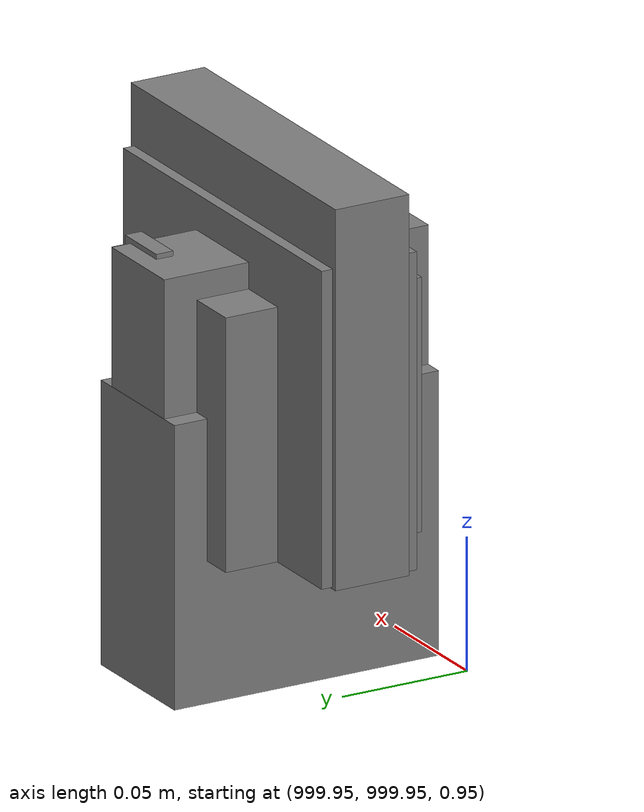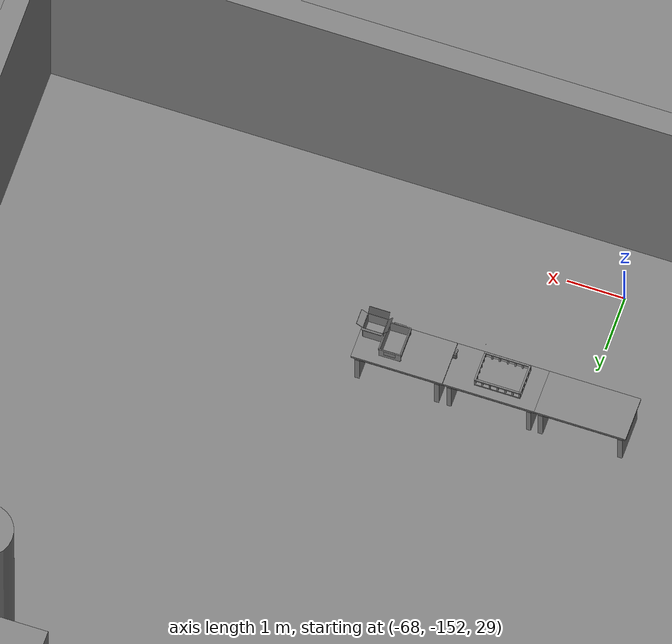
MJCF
<mujoco>
    <option gravity="0.000000000 0.000000000 -9.810000420" timestep="0.0049999999" integrator="implicitfast" density="1.225" viscosity="1.8000001e-05" noslip_iterations="10" iterations="100" sdf_iterations="50">
        <flag multiccd="disable"/>
    </option>
    <size memory="1000M"/>
    <compiler coordinate="local"/>
    <worldbody>
        <light cutoff="30" pos="0 1 1" dir="0 -1 -2"/>
        <light cutoff="30" pos="0 -1 1" dir="0 1 -2"/>
        <body pos="1000.000000000 1000.000000000 1.000000000" euler="0.000000000 0.000000000 180.000000000" name="openloong_gripper_2f85_fix_base_usda_battery_01">
            <geom contype="1" conaffinity="1" density="1000" type="box" material="" rgba="0.500000000 0.500000000 0.500000000 1.000000000" solimp="0.899999976 0.949999988 0.001000000" friction="1.000000000 0.005000000 0.000100000" solref="0.020000000 1.000000000" margin="0" condim="3" group="0" pos="-0.011123657 -0.041940309 0.101691343" quat="1.000000000 0.000000000 0.000000000 0.000000000" size="0.010800000 0.003375000 0.004725000" name="openloong_gripper_2f85_fix_base_usda_geom_7900D79E_94B2_474B_A00D_B18BB8B4479D"/>
            <geom contype="1" conaffinity="1" density="1000" type="box" material="" rgba="0.500000000 0.500000000 0.500000000 1.000000000" solimp="0.899999976 0.949999988 0.001000000" friction="1.000000000 0.005000000 0.000100000" solref="0.020000000 1.000000000" margin="0" condim="3" group="0" pos="-0.010876465 -0.044247437 0.047066893" quat="0.998702705 -0.050920475 0.000000000 0.000000000" size="0.009450001 0.002700000 0.024975000" name="openloong_gripper_2f85_fix_base_usda_geom_659F2653_D8B1_44DA_88CA_246A519DBA81"/>
            <geom contype="1" conaffinity="1" density="1000" type="box" material="" rgba="0.500000000 0.500000000 0.500000000 1.000000000" solimp="0.899999976 0.949999988 0.001000000" friction="1.000000000 0.005000000 0.000100000" solref="0.020000000 1.000000000" margin="0" condim="3" group="0" pos="-0.001235962 -0.000659180 0.047381196" quat="1.000000000 0.000000000 0.000000000 0.000000000" size="0.039420001 0.039150000 0.047250003" name="openloong_gripper_2f85_fix_base_usda_geom_32E27653_1C8B_4EB3_BC10_6F52F252FA6C"/>
            <geom contype="1" conaffinity="1" density="1000" type="box" material="" rgba="0.500000000 0.500000000 0.500000000 1.000000000" solimp="0.899999976 0.949999988 0.001000000" friction="1.000000000 0.005000000 0.000100000" solref="0.020000000 1.000000000" margin="0" condim="3" group="0" pos="-0.010876465 -0.039138794 0.009851727" quat="1.000000000 0.000000000 0.000000000 0.000000000" size="0.009450001 0.010800000 0.013500000" name="openloong_gripper_2f85_fix_base_usda_geom_94CD78FE_42E3_4713_9D5D_895B72FC2CC5"/>
            <geom contype="1" conaffinity="1" density="1000" type="box" material="" rgba="0.500000000 0.500000000 0.500000000 1.000000000" solimp="0.899999976 0.949999988 0.001000000" friction="1.000000000 0.005000000 0.000100000" solref="0.020000000 1.000000000" margin="0" condim="3" group="0" pos="-0.010876465 -0.041528322 0.071508206" quat="1.000000000 0.000000000 0.000000000 0.000000000" size="0.009450001 0.002700000 0.027000001" name="openloong_gripper_2f85_fix_base_usda_geom_68C42DB4_7FEC_4148_947F_927389881516"/>
            <freejoint name="openloong_gripper_2f85_fix_base_usda_battery_01_joint"/>
            <site size="0.005000000 0.005000000 0.005000000" rgba="0.500000000 0.500000000 0.500000000 1.000000000" pos="0.000000000 0.000000000 0.000000000" quat="0.999961913 0.008726500 0.000000000 0.000000000" group="0" type="sphere" name="openloong_gripper_2f85_fix_base_usda_battery_01site"/>
        </body>
        <body pos="1000.000000000 1000.000000000 1.000000000" euler="0.000011953 0.000005123 -179.999984741" name="openloong_gripper_2f85_fix_base_usda_intel_box">
            <geom contype="1" conaffinity="1" density="1000" type="box" material="" rgba="0.500000000 0.500000000 0.500000000 1.000000000" solimp="0.899999976 0.949999988 0.001000000" friction="1.000000000 0.005000000 0.000100000" solref="0.020000000 1.000000000" margin="0" condim="3" group="0" pos="0.000000000 -0.000067139 0.000082284" quat="0.707106709 0.000000225 0.000000253 0.707106650" size="0.052800003 0.025300000 0.052800003" name="openloong_gripper_2f85_fix_base_usda_geom_682C7526_40BF_49F3_8B59_D2B49B35F5EC"/>
            <freejoint name="openloong_gripper_2f85_fix_base_usda_intel_box_joint"/>
            <site size="0.005000000 0.005000000 0.005000000" rgba="0.500000000 0.500000000 0.500000000 1.000000000" pos="0.000000000 0.000000000 0.000000000" quat="0.999961913 0.008726500 0.000000000 0.000000000" group="0" type="sphere" name="openloong_gripper_2f85_fix_base_usda_intel_boxsite"/>
        </body>
        <body pos="-66.287460327 -148.981689453 31.164426804" euler="-69.964012146 -56.448066711 -95.009696960" mocap="true" name="spotlight3_SpotLight"/>
        <body pos="1000.000000000 1000.000000000 1.000000000" euler="0.000000000 0.000000000 180.000000000" name="openloong_gripper_2f85_fix_base_usda_wifi_box">
            <geom contype="1" conaffinity="1" density="1000" type="box" material="" rgba="0.500000000 0.500000000 0.500000000 1.000000000" solimp="0.899999976 0.949999988 0.001000000" friction="1.000000000 0.005000000 0.000100000" solref="0.020000000 1.000000000" margin="0" condim="3" group="0" pos="0.000000000 0.000000000 0.058978677" quat="0.000000000 0.000000047 0.000000000 1.000000000" size="0.068499997 0.018999999 0.059000000" name="openloong_gripper_2f85_fix_base_usda_geom_D25D1554_C2F1_48A7_9BD0_98FD6A603152"/>
            <freejoint name="openloong_gripper_2f85_fix_base_usda_wifi_box_joint"/>
            <site size="0.005000000 0.005000000 0.005000000" rgba="0.500000000 0.500000000 0.500000000 1.000000000" pos="0.000000000 0.000000000 0.000000000" quat="0.999961913 0.008726500 0.000000000 0.000000000" group="0" type="sphere" name="openloong_gripper_2f85_fix_base_usda_wifi_boxsite"/>
        </body>
        <body pos="1000.000000000 1000.000000000 1.000000000" euler="0.000000000 0.000000000 180.000000000" name="openloong_gripper_2f85_fix_base_usda_cpu_fan">
            <geom contype="1" conaffinity="1" density="1000" type="box" material="" rgba="0.500000000 0.500000000 0.500000000 1.000000000" solimp="0.899999976 0.949999988 0.001000000" friction="1.000000000 0.005000000 0.000100000" solref="0.020000000 1.000000000" margin="0" condim="3" group="0" pos="0.000000000 0.000000000 0.070034981" quat="0.000000000 0.000000000 0.000000000 1.000000000" size="0.070700005 0.014699999 0.070700005" name="openloong_gripper_2f85_fix_base_usda_geom_530F438C_C600_4B51_B08F_59A5302113B0"/>
            <freejoint name="openloong_gripper_2f85_fix_base_usda_cpu_fan_joint"/>
            <site size="0.005000000 0.005000000 0.005000000" rgba="0.500000000 0.500000000 0.500000000 1.000000000" pos="0.000000000 0.000000000 0.000000000" quat="0.999961913 0.008726535 0.000000000 0.000000000" group="0" type="sphere" name="openloong_gripper_2f85_fix_base_usda_cpu_fancsite"/>
        </body>
        <body pos="-66.073371887 -149.796112061 31.169874191" euler="-22.634765625 -23.614734650 -149.076004028" mocap="true" name="spotlight5_SpotLight"/>
        <body pos="1000.000000000 999.999938965 1.000000000" euler="0.000000000 0.000000000 180.000000000" name="openloong_gripper_2f85_fix_base_usda_intelcore_i5">
            <geom contype="1" conaffinity="1" density="1000" type="box" material="" rgba="0.500000000 0.500000000 0.500000000 1.000000000" solimp="0.899999976 0.949999988 0.001000000" friction="1.000000000 0.005000000 0.000100000" solref="0.020000000 1.000000000" margin="0" condim="3" group="0" pos="0.000000000 0.000000000 0.051722717" quat="0.707106709 0.000000000 0.000000000 -0.707106769" size="0.052800000 0.018080002 0.052800000" name="openloong_gripper_2f85_fix_base_usda_geom_D0427285_5982_4888_B11B_EA0EB3517374"/>
            <freejoint name="openloong_gripper_2f85_fix_base_usda_intelcore_i5_joint"/>
            <site size="0.005000000 0.005000000 0.005000000" rgba="0.500000000 0.500000000 0.500000000 1.000000000" pos="0.000000000 0.000000000 0.000000000" quat="0.999961913 0.008726534 0.000000000 0.000000000" group="0" type="sphere" name="openloong_gripper_2f85_fix_base_usda_intelcore_i5site"/>
        </body>
        <body pos="-66.162284851 -149.277999878 31.164356232" euler="31.780008316 59.341991425 -27.618738174" mocap="true" name="spotlight1_SpotLight"/>
        <body pos="-64.866622925 -149.383972168 30.183746338" euler="89.999984741 89.999946594 0.000000000" name="openloong_gripper_2f85_fix_base_usda_bluebox_01">
            <geom contype="1" conaffinity="1" density="1000" type="box" material="" rgba="0.500000000 0.500000000 0.500000000 1.000000000" solimp="0.899999976 0.949999988 0.001000000" friction="1.000000000 0.005000000 0.000100000" solref="0.020000000 1.000000000" margin="0" condim="3" group="0" pos="0.276580811 0.187225342 0.000068665" quat="0.707106948 0.000077471 0.707106352 0.000077486" size="0.100000001 0.057999998 0.010000000" name="openloong_gripper_2f85_fix_base_usda_geom_F2890A5D_F71B_49BC_B134_9344CF36AC79"/>
            <geom contype="1" conaffinity="1" density="1000" type="box" material="" rgba="0.500000000 0.500000000 0.500000000 1.000000000" solimp="0.899999976 0.949999988 0.001000000" friction="1.000000000 0.005000000 0.000100000" solref="0.020000000 1.000000000" margin="0" condim="3" group="0" pos="0.000000000 0.002883911 0.000000000" quat="0.999999881 0.000000000 0.000000000 0.000000000" size="0.254000008 0.003000000 0.172000006" name="openloong_gripper_2f85_fix_base_usda_geom_5225DE6D_B0A1_4FE1_B4EC_EBAA85E34712"/>
            <geom contype="1" conaffinity="1" density="1000" type="box" material="" rgba="0.500000000 0.500000000 0.500000000 1.000000000" solimp="0.899999976 0.949999988 0.001000000" friction="1.000000000 0.005000000 0.000100000" solref="0.020000000 1.000000000" margin="0" condim="3" group="0" pos="0.000000000 0.124874115 0.173484802" quat="0.999796331 0.020176515 -0.000000015 0.000000030" size="0.259999990 0.119999997 0.007000000" name="openloong_gripper_2f85_fix_base_usda_geom_AF0F578D_BC9E_4DFF_B7E1_43ABD94D39D6"/>
            <geom contype="1" conaffinity="1" density="1000" type="box" material="" rgba="0.500000000 0.500000000 0.500000000 1.000000000" solimp="0.899999976 0.949999988 0.001000000" friction="1.000000000 0.005000000 0.000100000" solref="0.020000000 1.000000000" margin="0" condim="3" group="0" pos="0.000000000 0.124874115 -0.173469543" quat="0.999796331 -0.020176545 -0.000000015 0.000000000" size="0.259999990 0.119999997 0.007000000" name="openloong_gripper_2f85_fix_base_usda_geom_1F676E91_F7DA_43B2_BE60_BF3C179D7B18"/>
            <geom contype="1" conaffinity="1" density="1000" type="box" material="" rgba="0.500000000 0.500000000 0.500000000 1.000000000" solimp="0.899999976 0.949999988 0.001000000" friction="1.000000000 0.005000000 0.000100000" solref="0.020000000 1.000000000" margin="0" condim="3" group="0" pos="0.000000000 0.214008331 0.188980103" quat="0.999912977 0.013176724 0.000000015 0.000000000" size="0.259999990 0.029999999 0.012500000" name="openloong_gripper_2f85_fix_base_usda_geom_D00E4AFD_AAD0_4946_8759_100426553E75"/>
            <geom contype="1" conaffinity="1" density="1000" type="box" material="" rgba="0.500000000 0.500000000 0.500000000 1.000000000" solimp="0.899999976 0.949999988 0.001000000" friction="1.000000000 0.005000000 0.000100000" solref="0.020000000 1.000000000" margin="0" condim="3" group="0" pos="-0.258361816 0.125289917 0.001876831" quat="0.702796936 -0.020792112 0.710783124 0.020769298" size="0.189999998 0.119999997 0.009000000" name="openloong_gripper_2f85_fix_base_usda_geom_5C95A9DF_33F7_4F86_BB7A_404AAEE96ED6"/>
            <geom contype="1" conaffinity="1" density="1000" type="box" material="" rgba="0.500000000 0.500000000 0.500000000 1.000000000" solimp="0.899999976 0.949999988 0.001000000" friction="1.000000000 0.005000000 0.000100000" solref="0.020000000 1.000000000" margin="0" condim="3" group="0" pos="0.000000000 0.214008331 -0.188980103" quat="0.999912977 -0.013176769 0.000000030 0.000000015" size="0.259999990 0.029999999 0.012500000" name="openloong_gripper_2f85_fix_base_usda_geom_56A29876_6888_4FCE_A5A6_C02DB84F8E9E"/>
            <geom contype="1" conaffinity="1" density="1000" type="box" material="" rgba="0.500000000 0.500000000 0.500000000 1.000000000" solimp="0.899999976 0.949999988 0.001000000" friction="1.000000000 0.005000000 0.000100000" solref="0.020000000 1.000000000" margin="0" condim="3" group="0" pos="-0.276611328 0.187225342 0.000068665" quat="0.707106650 0.000077441 0.707106709 0.000077456" size="0.100000001 0.057999998 0.010000000" name="openloong_gripper_2f85_fix_base_usda_geom_DBF3F77A_C422_4907_A833_1C7E463E8ED6"/>
            <geom contype="1" conaffinity="1" density="1000" type="box" material="" rgba="0.500000000 0.500000000 0.500000000 1.000000000" solimp="0.899999976 0.949999988 0.001000000" friction="1.000000000 0.005000000 0.000100000" solref="0.020000000 1.000000000" margin="0" condim="3" group="0" pos="0.258331299 0.125289917 0.001876831" quat="0.702851415 0.018856421 0.710823774 -0.019329369" size="0.189999998 0.119999997 0.009000000" name="openloong_gripper_2f85_fix_base_usda_geom_215791C3_8777_4255_8A49_FA5B0E4CD49B"/>
            <freejoint name="openloong_gripper_2f85_fix_base_usda_bluebox_01_joint"/>
            <site size="0.005000000 0.005000000 0.005000000" rgba="0.500000000 0.500000000 0.500000000 1.000000000" pos="0.000000000 0.000000000 0.000000000" quat="0.999961913 0.008726534 0.000000000 0.000000000" group="0" type="sphere" name="openloong_gripper_2f85_fix_base_usda_bluebox_01site"/>
        </body>
        <body pos="-64.496299744 -149.491867065 30.235729218" euler="0.000000000 0.000000000 89.999946594" name="openloong_gripper_2f85_fix_base_usda_cardboardbox_01">
            <geom contype="1" conaffinity="1" density="1000" type="box" material="" rgba="0.500000000 0.500000000 0.500000000 1.000000000" solimp="0.899999976 0.949999988 0.001000000" friction="1.000000000 0.005000000 0.000100000" solref="0.020000000 1.000000000" margin="0" condim="3" group="0" pos="-0.003166199 -0.004086494 0.005052090" quat="1.000000000 0.000000000 0.000000000 0.000000000" size="0.142499998 0.177500010 0.005000000" name="openloong_gripper_2f85_fix_base_usda_geom_5DEEC335_1F8E_4A2A_B5B1_78A1AFAEC8A4"/>
            <geom contype="1" conaffinity="1" density="1000" type="box" material="" rgba="0.500000000 0.500000000 0.500000000 1.000000000" solimp="0.899999976 0.949999988 0.001000000" friction="1.000000000 0.005000000 0.000100000" solref="0.020000000 1.000000000" margin="0" condim="3" group="0" pos="-0.003166199 0.170316696 0.150570869" quat="1.000000000 0.000000000 0.000000000 0.000000000" size="0.142499998 0.005000000 0.149999991" name="openloong_gripper_2f85_fix_base_usda_geom_A642CCAE_BF4D_4A67_AC86_1A71D5FD94B5"/>
            <geom contype="1" conaffinity="1" density="1000" type="box" material="" rgba="0.500000000 0.500000000 0.500000000 1.000000000" solimp="0.899999976 0.949999988 0.001000000" friction="1.000000000 0.005000000 0.000100000" solref="0.020000000 1.000000000" margin="0" condim="3" group="0" pos="-0.147399902 -0.005307198 0.150570869" quat="1.000000000 0.000000000 0.000000000 0.000000000" size="0.005000000 0.177500010 0.149999991" name="openloong_gripper_2f85_fix_base_usda_geom_4848114F_D588_4C8E_AFF7_26D22274981C"/>
            <geom contype="1" conaffinity="1" density="1000" type="box" material="" rgba="0.500000000 0.500000000 0.500000000 1.000000000" solimp="0.899999976 0.949999988 0.001000000" friction="1.000000000 0.005000000 0.000100000" solref="0.020000000 1.000000000" margin="0" condim="3" group="0" pos="0.140275955 -0.005307198 0.150570869" quat="1.000000000 0.000000000 0.000000000 0.000000000" size="0.005000000 0.177500010 0.149999991" name="openloong_gripper_2f85_fix_base_usda_geom_59424383_9B13_4628_9B7E_A3196D0711A0"/>
            <geom contype="1" conaffinity="1" density="1000" type="box" material="" rgba="0.500000000 0.500000000 0.500000000 1.000000000" solimp="0.899999976 0.949999988 0.001000000" friction="1.000000000 0.005000000 0.000100000" solref="0.020000000 1.000000000" margin="0" condim="3" group="0" pos="-0.003166199 -0.181550980 0.150570869" quat="1.000000000 0.000000000 0.000000000 0.000000000" size="0.142499998 0.005000000 0.149999991" name="openloong_gripper_2f85_fix_base_usda_geom_3DD69C4C_408A_4A28_AF21_16A11730BFE4"/>
            <freejoint name="openloong_gripper_2f85_fix_base_usda_cardboardbox_01_joint"/>
            <site size="0.005000000 0.005000000 0.005000000" rgba="0.500000000 0.500000000 0.500000000 1.000000000" pos="0.000000000 0.000000000 0.000000000" quat="0.999961913 0.008726535 0.000000000 0.000000000" group="0" type="sphere" name="openloong_gripper_2f85_fix_base_usda_site_DB3AAE18_4BD4_4093_B599_1C4CE3097BC3"/>
            <body pos="0.139160156 -0.004048347 0.301930904" euler="-179.999954224 49.383502960 179.999954224" name="openloong_gripper_2f85_fix_base_usda_A1_006">
                <geom contype="1" conaffinity="1" density="1000" type="box" material="" rgba="0.500000000 0.500000000 0.500000000 1.000000000" solimp="0.899999976 0.949999988 0.001000000" friction="1.000000000 0.005000000 0.000100000" solref="0.020000000 1.000000000" margin="0" condim="3" group="0" pos="-0.071587563 0.000009537 0.001745224" quat="0.999999881 0.000000000 0.000000000 0.000000000" size="0.071249999 0.179999992 0.002500000" name="openloong_gripper_2f85_fix_base_usda_geom_F03AB922_93D1_45B1_8D9E_19B7187FF4F9"/>
                <joint armature="0" stiffness="0.07" damping="0.0099999998" axis="0.000000 1.000000 0.000000" type="hinge" name="openloong_gripper_2f85_fix_base_usda_A1_006"/>
            </body>
            <body pos="-0.145902634 -0.004086494 0.301938057" euler="-180.000000000 -60.000011444 -180.000000000" name="openloong_gripper_2f85_fix_base_usda_A2_006">
                <geom contype="1" conaffinity="1" density="1000" type="box" material="" rgba="0.500000000 0.500000000 0.500000000 1.000000000" solimp="0.899999976 0.949999988 0.001000000" friction="1.000000000 0.005000000 0.000100000" solref="0.020000000 1.000000000" margin="0" condim="3" group="0" pos="0.071268082 0.000009537 0.002717972" quat="0.000002921 0.000000000 -0.000000030 0.999999881" size="0.071249999 0.179999992 0.002500000" name="openloong_gripper_2f85_fix_base_usda_geom_2A7B95AF_AEEC_44C5_B52E_B12B93803E4A"/>
                <joint armature="0" stiffness="0.07" damping="0.0099999998" axis="0.000000 1.000000 0.000000" type="hinge" name="openloong_gripper_2f85_fix_base_usda_A2_006"/>
            </body>
            <body pos="-0.003385544 0.175991058 0.301930904" euler="-125.858116150 -0.000004561 0.000002331" name="openloong_gripper_2f85_fix_base_usda_B2_006">
                <geom contype="1" conaffinity="1" density="1000" type="box" material="" rgba="0.500000000 0.500000000 0.500000000 1.000000000" solimp="0.899999976 0.949999988 0.001000000" friction="1.000000000 0.005000000 0.000100000" solref="0.020000000 1.000000000" margin="0" condim="3" group="0" pos="0.000009537 -0.070939064 -0.002470016" quat="0.999614120 0.027776197 -0.000000015 0.000000030" size="0.137500003 0.064999998 0.005000000" name="openloong_gripper_2f85_fix_base_usda_geom_FB78DDDD_8680_4FD2_A4D8_4FE9E3850E85"/>
                <joint armature="0" stiffness="0.07" damping="0.0099999998" axis="1.000000 0.000000 0.000000" type="hinge" name="openloong_gripper_2f85_fix_base_usda_B2_006"/>
            </body>
            <body pos="-0.003385544 -0.184140205 0.301938057" euler="147.805557251 0.000000000 0.000000000" name="openloong_gripper_2f85_fix_base_usda_B1_006">
                <geom contype="1" conaffinity="1" density="1000" type="box" material="" rgba="0.500000000 0.500000000 0.500000000 1.000000000" solimp="0.899999976 0.949999988 0.001000000" friction="1.000000000 0.005000000 0.000100000" solref="0.020000000 1.000000000" margin="0" condim="3" group="0" pos="-0.000028610 0.070202351 -0.002703667" quat="0.999614179 -0.027776167 0.000000000 0.000000000" size="0.137500003 0.064999998 0.005000000" name="openloong_gripper_2f85_fix_base_usda_geom_305B30C3_0D5E_468A_B3D6_FB88681DB53D"/>
                <joint armature="0" stiffness="0.07" damping="0.0099999998" axis="1.000000 0.000000 0.000000" type="hinge" name="openloong_gripper_2f85_fix_base_usda_B1_006"/>
            </body>
        </body>
        <body pos="-65.882858276 -149.481979370 30.229999542" euler="-64.487716675 0.000000000 0.000000000" name="openloong_gripper_2f85_fix_base_usda_Barcode">
            <geom contype="1" conaffinity="1" density="1000" type="box" material="" rgba="0.500000000 0.500000000 0.500000000 1.000000000" solimp="0.899999976 0.949999988 0.001000000" friction="1.000000000 0.005000000 0.000100000" solref="0.020000000 1.000000000" margin="0" condim="3" group="0" pos="0.000000000 0.013038635 0.001419067" quat="0.000000000 0.000000000 0.000000000 1.000000119" size="0.034000002 0.010000000 0.017999999" name="openloong_gripper_2f85_fix_base_usda_geom_70B033AE_3DE4_4750_B549_C1C6B2C070CB"/>
            <geom contype="1" conaffinity="1" density="1000" type="box" material="" rgba="0.500000000 0.500000000 0.500000000 1.000000000" solimp="0.899999976 0.949999988 0.001000000" friction="1.000000000 0.005000000 0.000100000" solref="0.020000000 1.000000000" margin="0" condim="3" group="0" pos="0.000000000 -0.035301208 -0.007095337" quat="0.000000000 0.000000000 -0.043619365 0.999048233" size="0.028999999 0.010000000 0.020000000" name="openloong_gripper_2f85_fix_base_usda_geom_2F11D902_937E_41FA_80C9_E70F5D4A2C1C"/>
            <geom contype="1" conaffinity="1" density="1000" type="box" material="" rgba="0.500000000 0.500000000 0.500000000 1.000000000" solimp="0.899999976 0.949999988 0.001000000" friction="1.000000000 0.005000000 0.000100000" solref="0.020000000 1.000000000" margin="0" condim="3" group="0" pos="0.000000000 -0.043411255 -0.011749268" quat="0.922262907 0.386563420 0.000000000 0.000000000" size="0.026000001 0.010000000 0.020000000" name="openloong_gripper_2f85_fix_base_usda_geom_3987E9BA_F189_40B1_83B5_BEECFFD263FE"/>
            <geom contype="1" conaffinity="1" density="1000" type="box" material="" rgba="0.500000000 0.500000000 0.500000000 1.000000000" solimp="0.899999976 0.949999988 0.001000000" friction="1.000000000 0.005000000 0.000100000" solref="0.020000000 1.000000000" margin="0" condim="3" group="0" pos="0.000000000 -0.016967773 -0.031860352" quat="0.000000000 0.000000000 0.000000000 1.000000119" size="0.008000000 0.010000000 0.013000000" name="openloong_gripper_2f85_fix_base_usda_geom_9945C944_DE29_44A4_8EF0_CC44DE29AFA1"/>
            <geom contype="1" conaffinity="1" density="1000" type="box" material="" rgba="0.500000000 0.500000000 0.500000000 1.000000000" solimp="0.899999976 0.949999988 0.001000000" friction="1.000000000 0.005000000 0.000100000" solref="0.020000000 1.000000000" margin="0" condim="3" group="0" pos="0.000000000 -0.001869202 0.000312805" quat="0.953716993 0.300705761 0.000000000 0.000000000" size="0.032000002 0.010000000 0.018999999" name="openloong_gripper_2f85_fix_base_usda_geom_088E18ED_B7F2_4EC1_B053_BB12B75FAED6"/>
            <geom contype="1" conaffinity="1" density="1000" type="box" material="" rgba="0.500000000 0.500000000 0.500000000 1.000000000" solimp="0.899999976 0.949999988 0.001000000" friction="1.000000000 0.005000000 0.000100000" solref="0.020000000 1.000000000" margin="0" condim="3" group="0" pos="0.000000000 -0.019531250 -0.003173828" quat="0.953716993 0.300705761 0.000000000 0.000000000" size="0.030999999 0.010000000 0.020000000" name="openloong_gripper_2f85_fix_base_usda_geom_1F774635_58A7_486C_8753_2FB01D933915"/>
            <geom contype="1" conaffinity="1" density="1000" type="box" material="" rgba="0.500000000 0.500000000 0.500000000 1.000000000" solimp="0.899999976 0.949999988 0.001000000" friction="1.000000000 0.005000000 0.000100000" solref="0.020000000 1.000000000" margin="0" condim="3" group="0" pos="0.000000000 -0.035301208 -0.007095337" quat="0.953716993 0.300705761 0.000000000 0.000000000" size="0.028999999 0.010000000 0.020000000" name="openloong_gripper_2f85_fix_base_usda_geom_9F3A279A_FE5C_4DCD_AF16_2E1313598DE4"/>
            <geom contype="1" conaffinity="1" density="1000" type="box" material="" rgba="0.500000000 0.500000000 0.500000000 1.000000000" solimp="0.899999976 0.949999988 0.001000000" friction="1.000000000 0.005000000 0.000100000" solref="0.020000000 1.000000000" margin="0" condim="3" group="0" pos="0.000000000 -0.042617798 -0.071121216" quat="0.000000000 0.000000000 0.000000000 1.000000119" size="0.013000000 0.021000000 0.059999999" name="openloong_gripper_2f85_fix_base_usda_geom_B6FA77FC_DA9A_479B_8BCC_A5AE4C68BBD4"/>
            <freejoint name="openloong_gripper_2f85_fix_base_usda_Barcode_joint"/>
            <site size="0.005000000 0.005000000 0.005000000" rgba="0.500000000 0.500000000 0.500000000 1.000000000" pos="0.000000000 0.000000000 0.000000000" quat="1.000000000 0.000000000 0.000000000 0.000000000" group="0" type="sphere" name="openloong_gripper_2f85_fix_base_usda_Barcode_site"/>
        </body>
        <body pos="-66.745018005 -149.392349243 30.184000015" euler="0.000000000 0.000000000 89.999946594" name="[22331411554243]_Basket_01">
            <geom contype="1" conaffinity="1" density="1000" type="box" material="" rgba="0.500000000 0.500000000 0.500000000 1.000000000" solimp="0.899999976 0.949999988 0.001000000" friction="1.000000000 0.005000000 0.000100000" solref="0.020000000 1.000000000" margin="0" condim="3" group="0" pos="-0.052425385 0.389207840 0.089787483" quat="0.707107008 0.000000000 0.000000000 0.707106411" size="0.014249999 0.014249999 0.059999999" name="[22331411554243]_geom_DDCB79B1_CD41_467C_B3BF_3DD85908D6FB"/>
            <geom contype="1" conaffinity="1" density="1000" type="box" material="" rgba="0.500000000 0.500000000 0.500000000 1.000000000" solimp="0.899999976 0.949999988 0.001000000" friction="1.000000000 0.005000000 0.000100000" solref="0.020000000 1.000000000" margin="0" condim="3" group="0" pos="0.264015198 -0.133043289 0.089787483" quat="0.707107008 0.000000000 0.000000000 0.707106411" size="0.014249999 0.014249999 0.059999999" name="[22331411554243]_geom_F09EE845_9B06_423F_B6A7_772FAE119C4E"/>
            <geom contype="1" conaffinity="1" density="1000" type="box" material="" rgba="0.500000000 0.500000000 0.500000000 1.000000000" solimp="0.899999976 0.949999988 0.001000000" friction="1.000000000 0.005000000 0.000100000" solref="0.020000000 1.000000000" margin="0" condim="3" group="0" pos="-0.264015198 -0.265548706 0.089793205" quat="0.707107008 0.000000000 0.000000000 0.707106411" size="0.014249999 0.014249999 0.059999999" name="[22331411554243]_geom_C23FB457_C71A_450F_9A8B_E5009D2DF6C3"/>
            <geom contype="1" conaffinity="1" density="1000" type="box" material="" rgba="0.500000000 0.500000000 0.500000000 1.000000000" solimp="0.899999976 0.949999988 0.001000000" friction="1.000000000 0.005000000 0.000100000" solref="0.020000000 1.000000000" margin="0" condim="3" group="0" pos="-0.160263062 -0.389322281 0.089793205" quat="0.707107008 0.000000000 0.000000000 0.707106411" size="0.014249999 0.014249999 0.059999999" name="[22331411554243]_geom_6E96CE2D_08AF_435A_A948_A56A97F7FB07"/>
            <geom contype="1" conaffinity="1" density="1000" type="box" material="" rgba="0.500000000 0.500000000 0.500000000 1.000000000" solimp="0.899999976 0.949999988 0.001000000" friction="1.000000000 0.005000000 0.000100000" solref="0.020000000 1.000000000" margin="0" condim="3" group="0" pos="0.162265778 -0.389322281 0.089787483" quat="0.707107008 0.000000000 0.000000000 0.707106411" size="0.014249999 0.014249999 0.059999999" name="[22331411554243]_geom_3DA03BEA_0701_44D8_AA5B_E7CBE7E99F21"/>
            <geom contype="1" conaffinity="1" density="1000" type="box" material="" rgba="0.500000000 0.500000000 0.500000000 1.000000000" solimp="0.899999976 0.949999988 0.001000000" friction="1.000000000 0.005000000 0.000100000" solref="0.020000000 1.000000000" margin="0" condim="3" group="0" pos="0.264015198 0.389207840 0.089787483" quat="0.707107008 0.000000000 0.000000000 0.707106411" size="0.014249999 0.014249999 0.059999999" name="[22331411554243]_geom_DE88D6FE_F60E_43B7_8E53_BDEE76FE4A3E"/>
            <geom contype="1" conaffinity="1" density="1000" type="box" material="" rgba="0.500000000 0.500000000 0.500000000 1.000000000" solimp="0.899999976 0.949999988 0.001000000" friction="1.000000000 0.005000000 0.000100000" solref="0.020000000 1.000000000" margin="0" condim="3" group="0" pos="-0.264015198 -0.133043289 0.089793205" quat="0.707107008 0.000000000 0.000000000 0.707106411" size="0.014249999 0.014249999 0.059999999" name="[22331411554243]_geom_D6DFE292_B3FF_4418_9259_2E9EF1C164FF"/>
            <geom contype="1" conaffinity="1" density="1000" type="box" material="" rgba="0.500000000 0.500000000 0.500000000 1.000000000" solimp="0.899999976 0.949999988 0.001000000" friction="1.000000000 0.005000000 0.000100000" solref="0.020000000 1.000000000" margin="0" condim="3" group="0" pos="-0.264026642 0.269256592 0.089793205" quat="0.707107008 0.000000000 0.000000000 0.707106411" size="0.014249999 0.014249999 0.059999999" name="[22331411554243]_geom_8B3BFEB8_F893_40F2_9D98_F6C7FEE25244"/>
            <geom contype="1" conaffinity="1" density="1000" type="box" material="" rgba="0.500000000 0.500000000 0.500000000 1.000000000" solimp="0.899999976 0.949999988 0.001000000" friction="1.000000000 0.005000000 0.000100000" solref="0.020000000 1.000000000" margin="0" condim="3" group="0" pos="0.054462433 0.389207840 0.089787483" quat="0.707107008 0.000000000 0.000000000 0.707106411" size="0.014249999 0.014249999 0.059999999" name="[22331411554243]_geom_CE72BBA1_6C87_4521_B365_5ECEF3EE792F"/>
            <geom contype="1" conaffinity="1" density="1000" type="box" material="" rgba="0.500000000 0.500000000 0.500000000 1.000000000" solimp="0.899999976 0.949999988 0.001000000" friction="1.000000000 0.005000000 0.000100000" solref="0.020000000 1.000000000" margin="0" condim="3" group="0" pos="0.054462433 -0.389322281 0.089787483" quat="0.707107008 0.000000000 0.000000000 0.707106411" size="0.014249999 0.014249999 0.059999999" name="[22331411554243]_geom_78C8112D_8A17_4A9F_BE6E_77CCF6DD88D2"/>
            <geom contype="1" conaffinity="1" density="1000" type="box" material="" rgba="0.500000000 0.500000000 0.500000000 1.000000000" solimp="0.899999976 0.949999988 0.001000000" friction="1.000000000 0.005000000 0.000100000" solref="0.020000000 1.000000000" margin="0" condim="3" group="0" pos="0.264015198 0.269256592 0.089793205" quat="0.707107008 0.000000000 0.000000000 0.707106411" size="0.014249999 0.014249999 0.059999999" name="[22331411554243]_geom_B3458805_7E38_4D25_940C_521C0415119F"/>
            <geom contype="1" conaffinity="1" density="1000" type="box" material="" rgba="0.500000000 0.500000000 0.500000000 1.000000000" solimp="0.899999976 0.949999988 0.001000000" friction="1.000000000 0.005000000 0.000100000" solref="0.020000000 1.000000000" margin="0" condim="3" group="0" pos="0.264015198 -0.389322281 0.089787483" quat="0.707107008 0.000000000 0.000000000 0.707106411" size="0.014249999 0.014249999 0.059999999" name="[22331411554243]_geom_002FE7D2_5CA4_4C35_94F8_7ACE61ACF10D"/>
            <geom contype="1" conaffinity="1" density="1000" type="box" material="" rgba="0.500000000 0.500000000 0.500000000 1.000000000" solimp="0.899999976 0.949999988 0.001000000" friction="1.000000000 0.005000000 0.000100000" solref="0.020000000 1.000000000" margin="0" condim="3" group="0" pos="0.000000000 0.000000000 0.015998840" quat="0.707107008 0.000000000 0.000000000 0.707106411" size="0.403499991 0.279000014 0.015750000" name="[22331411554243]_geom_03079A82_306B_4AF2_8394_93790BAE6260"/>
            <geom contype="1" conaffinity="1" density="1000" type="box" material="" rgba="0.500000000 0.500000000 0.500000000 1.000000000" solimp="0.899999976 0.949999988 0.001000000" friction="1.000000000 0.005000000 0.000100000" solref="0.020000000 1.000000000" margin="0" condim="3" group="0" pos="0.000000000 -0.389476776 0.163619041" quat="0.707107008 0.000000000 0.000000000 0.707106411" size="0.015000000 0.277500004 0.015750000" name="[22331411554243]_geom_FE1B7533_662D_440A_A23E_D3ECE5D437C9"/>
            <geom contype="1" conaffinity="1" density="1000" type="box" material="" rgba="0.500000000 0.500000000 0.500000000 1.000000000" solimp="0.899999976 0.949999988 0.001000000" friction="1.000000000 0.005000000 0.000100000" solref="0.020000000 1.000000000" margin="0" condim="3" group="0" pos="0.162265778 0.389207840 0.089787483" quat="0.707107008 0.000000000 0.000000000 0.707106411" size="0.014249999 0.014249999 0.059999999" name="[22331411554243]_geom_67E8481A_2EB5_44E8_8696_47B7601D7CA1"/>
            <geom contype="1" conaffinity="1" density="1000" type="box" material="" rgba="0.500000000 0.500000000 0.500000000 1.000000000" solimp="0.899999976 0.949999988 0.001000000" friction="1.000000000 0.005000000 0.000100000" solref="0.020000000 1.000000000" margin="0" condim="3" group="0" pos="0.000000000 0.389471054 0.163619041" quat="0.707107008 0.000000000 0.000000000 0.707106411" size="0.015000000 0.277500004 0.015750000" name="[22331411554243]_geom_DFBE239B_A364_48F6_81F5_0FC25D0CCA76"/>
            <geom contype="1" conaffinity="1" density="1000" type="box" material="" rgba="0.500000000 0.500000000 0.500000000 1.000000000" solimp="0.899999976 0.949999988 0.001000000" friction="1.000000000 0.005000000 0.000100000" solref="0.020000000 1.000000000" margin="0" condim="3" group="0" pos="-0.263511658 0.000000000 0.163619041" quat="0.707107008 0.000000000 0.000000000 0.707106411" size="0.403499991 0.015000000 0.015750000" name="[22331411554243]_geom_6A00A7EB_64C8_4DD9_B706_F11C91DDC785"/>
            <geom contype="1" conaffinity="1" density="1000" type="box" material="" rgba="0.500000000 0.500000000 0.500000000 1.000000000" solimp="0.899999976 0.949999988 0.001000000" friction="1.000000000 0.005000000 0.000100000" solref="0.020000000 1.000000000" margin="0" condim="3" group="0" pos="-0.264015198 0.141334534 0.089793205" quat="0.707107008 0.000000000 0.000000000 0.707106411" size="0.014249999 0.014249999 0.059999999" name="[22331411554243]_geom_FBF33B52_78A7_466B_9519_394BA8EAD024"/>
            <geom contype="1" conaffinity="1" density="1000" type="box" material="" rgba="0.500000000 0.500000000 0.500000000 1.000000000" solimp="0.899999976 0.949999988 0.001000000" friction="1.000000000 0.005000000 0.000100000" solref="0.020000000 1.000000000" margin="0" condim="3" group="0" pos="0.264015198 -0.265548706 0.089787483" quat="0.707107008 0.000000000 0.000000000 0.707106411" size="0.014249999 0.014249999 0.059999999" name="[22331411554243]_geom_32EACEF7_20C7_4466_81ED_DACE26ABB2AC"/>
            <geom contype="1" conaffinity="1" density="1000" type="box" material="" rgba="0.500000000 0.500000000 0.500000000 1.000000000" solimp="0.899999976 0.949999988 0.001000000" friction="1.000000000 0.005000000 0.000100000" solref="0.020000000 1.000000000" margin="0" condim="3" group="0" pos="-0.160263062 0.389207840 0.089787483" quat="0.707107008 0.000000000 0.000000000 0.707106411" size="0.014249999 0.014249999 0.059999999" name="[22331411554243]_geom_A0D9C66E_39C9_481C_8647_A986FC6CC4BC"/>
            <geom contype="1" conaffinity="1" density="1000" type="box" material="" rgba="0.500000000 0.500000000 0.500000000 1.000000000" solimp="0.899999976 0.949999988 0.001000000" friction="1.000000000 0.005000000 0.000100000" solref="0.020000000 1.000000000" margin="0" condim="3" group="0" pos="-0.052425385 -0.389322281 0.089787483" quat="0.707107008 0.000000000 0.000000000 0.707106411" size="0.014249999 0.014249999 0.059999999" name="[22331411554243]_geom_57E2B678_CD58_43DF_BD62_115522E71D4E"/>
            <geom contype="1" conaffinity="1" density="1000" type="box" material="" rgba="0.500000000 0.500000000 0.500000000 1.000000000" solimp="0.899999976 0.949999988 0.001000000" friction="1.000000000 0.005000000 0.000100000" solref="0.020000000 1.000000000" margin="0" condim="3" group="0" pos="-0.264026642 -0.389322281 0.089793205" quat="0.707107008 0.000000000 0.000000000 0.707106411" size="0.014249999 0.014249999 0.059999999" name="[22331411554243]_geom_0D29CD86_DBF2_4149_8BC9_40AF46E0774C"/>
            <geom contype="1" conaffinity="1" density="1000" type="box" material="" rgba="0.500000000 0.500000000 0.500000000 1.000000000" solimp="0.899999976 0.949999988 0.001000000" friction="1.000000000 0.005000000 0.000100000" solref="0.020000000 1.000000000" margin="0" condim="3" group="0" pos="0.264015198 0.141334534 0.089787483" quat="0.707107008 0.000000000 0.000000000 0.707106411" size="0.014249999 0.014249999 0.059999999" name="[22331411554243]_geom_B03E9FF7_C3FF_484F_A450_D08734FDABFA"/>
            <geom contype="1" conaffinity="1" density="1000" type="box" material="" rgba="0.500000000 0.500000000 0.500000000 1.000000000" solimp="0.899999976 0.949999988 0.001000000" friction="1.000000000 0.005000000 0.000100000" solref="0.020000000 1.000000000" margin="0" condim="3" group="0" pos="-0.264015198 0.389207840 0.089793205" quat="0.707107008 0.000000000 0.000000000 0.707106411" size="0.014249999 0.014249999 0.059999999" name="[22331411554243]_geom_990A861A_230A_4F43_90A1_523FB3F584E8"/>
            <geom contype="1" conaffinity="1" density="1000" type="box" material="" rgba="0.500000000 0.500000000 0.500000000 1.000000000" solimp="0.899999976 0.949999988 0.001000000" friction="1.000000000 0.005000000 0.000100000" solref="0.020000000 1.000000000" margin="0" condim="3" group="0" pos="0.264015198 0.004480362 0.089787483" quat="0.707107008 0.000000000 0.000000000 0.707106411" size="0.014249999 0.014249999 0.059999999" name="[22331411554243]_geom_1294A1E6_D0C9_4C88_B672_35163112CA89"/>
            <geom contype="1" conaffinity="1" density="1000" type="box" material="" rgba="0.500000000 0.500000000 0.500000000 1.000000000" solimp="0.899999976 0.949999988 0.001000000" friction="1.000000000 0.005000000 0.000100000" solref="0.020000000 1.000000000" margin="0" condim="3" group="0" pos="0.263694763 -0.000011444 0.163619041" quat="0.707107008 0.000000000 0.000000000 0.707106411" size="0.403499991 0.015000000 0.015750000" name="[22331411554243]_geom_40C64B53_A9B5_4755_B869_B81A4F2D3D71"/>
            <geom contype="1" conaffinity="1" density="1000" type="box" material="" rgba="0.500000000 0.500000000 0.500000000 1.000000000" solimp="0.899999976 0.949999988 0.001000000" friction="1.000000000 0.005000000 0.000100000" solref="0.020000000 1.000000000" margin="0" condim="3" group="0" pos="-0.264015198 0.004480362 0.089793205" quat="0.707107008 0.000000000 0.000000000 0.707106411" size="0.014249999 0.014249999 0.059999999" name="[22331411554243]_geom_05CDAEE6_2C25_4245_B0AD_69CA380CE06D"/>
            <freejoint name="[22331411554243]_joint_15696C04_AD78_4545_88C2_27E44CACD027"/>
        </body>
        <body pos="0.000000000 0.000000000 0.000000000" euler="0.000000000 0.000000000 0.000000000" name="Static Objects_Static Objects">
            <geom contype="1" conaffinity="1" density="1000" type="box" material="" rgba="0.500000000 0.500000000 0.500000000 1.000000000" solimp="0.899999976 0.949999988 0.001000000" friction="1.000000000 0.005000000 0.000100000" solref="0.020000000 1.000000000" margin="0" condim="3" group="0" pos="-67.544113159 -149.365814209 29.727830887" quat="0.500000417 0.499999970 0.499999553 0.499999970" size="0.381000012 0.319999993 0.041000001" name="Static Objects_geom_F1D8FD94_D442_46C9_8531_4755D4ECEACF"/>
            <geom contype="1" conaffinity="1" density="1000" type="box" material="" rgba="0.500000000 0.500000000 0.500000000 1.000000000" solimp="0.899999976 0.949999988 0.001000000" friction="1.000000000 0.005000000 0.000100000" solref="0.020000000 1.000000000" margin="0" condim="3" group="0" pos="-68.239501953 -149.365814209 30.086868286" quat="0.500000417 0.499999970 0.499999553 0.499999970" size="0.370999992 0.039500002 0.745000005" name="Static Objects_geom_4DB900F9_F5F5_41A9_82FD_63E6E5B3314F"/>
            <geom contype="1" conaffinity="1" density="1000" type="box" material="" rgba="0.500000000 0.500000000 0.500000000 1.000000000" solimp="0.899999976 0.949999988 0.001000000" friction="1.000000000 0.005000000 0.000100000" solref="0.020000000 1.000000000" margin="0" condim="3" group="0" pos="-68.239501953 -149.365814209 30.147235870" quat="0.500000417 0.499999970 0.499999553 0.499999970" size="0.400000006 0.022000000 0.800000012" name="Static Objects_geom_0A38FFEE_4289_466A_B816_8CCB53FBACA3"/>
            <geom contype="1" conaffinity="1" density="1000" type="box" material="" rgba="0.500000000 0.500000000 0.500000000 1.000000000" solimp="0.899999976 0.949999988 0.001000000" friction="1.000000000 0.005000000 0.000100000" solref="0.020000000 1.000000000" margin="0" condim="3" group="0" pos="-68.934890747 -149.365814209 29.727830887" quat="0.500000417 0.499999970 0.499999553 0.499999970" size="0.381000012 0.319999993 0.041000001" name="Static Objects_geom_01A82152_846D_4CF3_AEB8_A66308F45F78"/>
            <geom contype="1" conaffinity="1" density="1000" type="box" material="" rgba="0.500000000 0.500000000 0.500000000 1.000000000" solimp="0.899999976 0.949999988 0.001000000" friction="1.000000000 0.005000000 0.000100000" solref="0.020000000 1.000000000" margin="0" condim="3" group="0" pos="-68.239501953 -149.365814209 29.561563492" quat="0.500000417 0.499999970 0.499999553 0.499999970" size="0.020000000 0.022000000 0.660000026" name="Static Objects_geom_4ED5C16E_8584_4489_BB00_97138F4C37B4"/>
            <geom contype="1" conaffinity="1" density="1000" type="box" material="" rgba="0.500000000 0.500000000 0.500000000 1.000000000" solimp="0.899999976 0.949999988 0.001000000" friction="1.000000000 0.005000000 0.000100000" solref="0.020000000 1.000000000" margin="0" condim="3" group="0" pos="-65.945671082 -149.365814209 29.727830887" quat="0.500000417 0.499999970 0.499999553 0.499999970" size="0.381000012 0.319999993 0.041000001" name="Static Objects_geom_5E5CB340_76F4_4B3E_8F98_87C4BEDC4342"/>
            <geom contype="1" conaffinity="1" density="1000" type="box" material="" rgba="0.500000000 0.500000000 0.500000000 1.000000000" solimp="0.899999976 0.949999988 0.001000000" friction="1.000000000 0.005000000 0.000100000" solref="0.020000000 1.000000000" margin="0" condim="3" group="0" pos="-66.641059875 -149.365814209 30.086868286" quat="0.500000417 0.499999970 0.499999553 0.499999970" size="0.370999992 0.039500002 0.745000005" name="Static Objects_geom_68063308_244C_4BA3_9FB8_96A96EA629ED"/>
            <geom contype="1" conaffinity="1" density="1000" type="box" material="" rgba="0.500000000 0.500000000 0.500000000 1.000000000" solimp="0.899999976 0.949999988 0.001000000" friction="1.000000000 0.005000000 0.000100000" solref="0.020000000 1.000000000" margin="0" condim="3" group="0" pos="-66.641059875 -149.365814209 30.147235870" quat="0.500000417 0.499999970 0.499999553 0.499999970" size="0.400000006 0.022000000 0.800000012" name="Static Objects_geom_7DC8990C_4D29_4E66_82E6_C22DD948A320"/>
            <geom contype="1" conaffinity="1" density="1000" type="box" material="" rgba="0.500000000 0.500000000 0.500000000 1.000000000" solimp="0.899999976 0.949999988 0.001000000" friction="1.000000000 0.005000000 0.000100000" solref="0.020000000 1.000000000" margin="0" condim="3" group="0" pos="-67.336448669 -149.365814209 29.727830887" quat="0.500000417 0.499999970 0.499999553 0.499999970" size="0.381000012 0.319999993 0.041000001" name="Static Objects_geom_64FD254F_9589_4030_888C_63E5715F15D1"/>
            <geom contype="1" conaffinity="1" density="1000" type="box" material="" rgba="0.500000000 0.500000000 0.500000000 1.000000000" solimp="0.899999976 0.949999988 0.001000000" friction="1.000000000 0.005000000 0.000100000" solref="0.020000000 1.000000000" margin="0" condim="3" group="0" pos="-66.641059875 -149.365814209 29.561563492" quat="0.500000417 0.499999970 0.499999553 0.499999970" size="0.020000000 0.022000000 0.660000026" name="Static Objects_geom_B6192DEC_F42C_4B87_B5D3_D6543B418582"/>
            <geom contype="1" conaffinity="1" density="1000" type="box" material="" rgba="0.500000000 0.500000000 0.500000000 1.000000000" solimp="0.899999976 0.949999988 0.001000000" friction="1.000000000 0.005000000 0.000100000" solref="0.020000000 1.000000000" margin="0" condim="3" group="0" pos="-64.338577271 -149.365814209 29.727830887" quat="0.500000417 0.499999970 0.499999553 0.499999970" size="0.381000012 0.319999993 0.041000001" name="Static Objects_geom_A4A20878_BCF9_4FFB_9D0D_41D1157CBAA5"/>
            <geom contype="1" conaffinity="1" density="1000" type="box" material="" rgba="0.500000000 0.500000000 0.500000000 1.000000000" solimp="0.899999976 0.949999988 0.001000000" friction="1.000000000 0.005000000 0.000100000" solref="0.020000000 1.000000000" margin="0" condim="3" group="0" pos="-65.033966064 -149.365814209 30.086868286" quat="0.500000417 0.499999970 0.499999553 0.499999970" size="0.370999992 0.039500002 0.745000005" name="Static Objects_geom_FEA712FF_309C_4594_A13C_0AED7CEAA7C1"/>
            <geom contype="1" conaffinity="1" density="1000" type="box" material="" rgba="0.500000000 0.500000000 0.500000000 1.000000000" solimp="0.899999976 0.949999988 0.001000000" friction="1.000000000 0.005000000 0.000100000" solref="0.020000000 1.000000000" margin="0" condim="3" group="0" pos="-65.033966064 -149.365814209 30.147235870" quat="0.500000417 0.499999970 0.499999553 0.499999970" size="0.400000006 0.022000000 0.800000012" name="Static Objects_geom_3EE61C30_F14F_4EB1_93F3_5666F3E450F5"/>
            <geom contype="1" conaffinity="1" density="1000" type="box" material="" rgba="0.500000000 0.500000000 0.500000000 1.000000000" solimp="0.899999976 0.949999988 0.001000000" friction="1.000000000 0.005000000 0.000100000" solref="0.020000000 1.000000000" margin="0" condim="3" group="0" pos="-65.729354858 -149.365814209 29.727830887" quat="0.500000417 0.499999970 0.499999553 0.499999970" size="0.381000012 0.319999993 0.041000001" name="Static Objects_geom_6A959D70_6536_4E75_AAFB_791704ACCAC5"/>
            <geom contype="1" conaffinity="1" density="1000" type="box" material="" rgba="0.500000000 0.500000000 0.500000000 1.000000000" solimp="0.899999976 0.949999988 0.001000000" friction="1.000000000 0.005000000 0.000100000" solref="0.020000000 1.000000000" margin="0" condim="3" group="0" pos="-65.033966064 -149.365814209 29.561563492" quat="0.500000417 0.499999970 0.499999553 0.499999970" size="0.020000000 0.022000000 0.660000026" name="Static Objects_geom_C5B76082_140E_4EAB_A7C2_ADA2665B837A"/>
            <geom contype="1" conaffinity="1" density="1000" type="box" material="" rgba="0.500000000 0.500000000 0.500000000 1.000000000" solimp="0.899999976 0.949999988 0.001000000" friction="1.000000000 0.005000000 0.000100000" solref="0.020000000 1.000000000" margin="0" condim="3" group="0" pos="-61.754566193 -137.853729248 33.906845093" quat="0.707107067 0.000000000 0.000000000 0.707106471" size="0.759999990 0.759999990 4.500000000" name="Static Objects_geom_3ECED1F0_6A93_4109_B2CA_202E06BF5661"/>
            <geom contype="1" conaffinity="1" density="1000" type="box" material="" rgba="0.500000000 0.500000000 0.500000000 1.000000000" solimp="0.899999976 0.949999988 0.001000000" friction="1.000000000 0.005000000 0.000100000" solref="0.020000000 1.000000000" margin="0" condim="3" group="0" pos="-57.511135101 -144.927108765 31.707921982" quat="1.000000000 0.000000000 0.000000000 0.000000000" size="0.200000003 8.000000000 2.299999952" name="Static Objects_geom_48865E15_E329_4BCD_A5F0_DCFE87A5FA4F"/>
            <geom contype="1" conaffinity="1" density="1000" type="box" material="" rgba="0.500000000 0.500000000 0.500000000 1.000000000" solimp="0.899999976 0.949999988 0.001000000" friction="1.000000000 0.005000000 0.000100000" solref="0.020000000 1.000000000" margin="0" condim="3" group="0" pos="-80.517646790 -157.574050903 31.688196182" quat="0.707107067 0.000000000 0.000000000 0.707106471" size="0.600000024 0.600000024 2.299999952" name="Static Objects_geom_14D2C349_BD05_4695_A525_D4BCCD50FEA5"/>
            <geom contype="1" conaffinity="1" density="1000" type="box" material="" rgba="0.500000000 0.500000000 0.500000000 1.000000000" solimp="0.899999976 0.949999988 0.001000000" friction="1.000000000 0.005000000 0.000100000" solref="0.020000000 1.000000000" margin="0" condim="3" group="0" pos="-80.711044312 -147.414932251 31.666158676" quat="1.000000000 0.000000000 0.000000000 0.000000000" size="0.200000003 10.000000000 2.299999952" name="Static Objects_geom_093F1C8B_0430_4EFC_BFD4_A066395C6A77"/>
            <geom contype="1" conaffinity="1" density="1000" type="box" material="" rgba="0.500000000 0.500000000 0.500000000 1.000000000" solimp="0.899999976 0.949999988 0.001000000" friction="1.000000000 0.005000000 0.000100000" solref="0.020000000 1.000000000" margin="0" condim="3" group="0" pos="-57.687217712 -137.434692383 31.688196182" quat="0.707107067 0.000000000 0.000000000 0.707106471" size="0.600000024 0.600000024 2.299999952" name="Static Objects_geom_F53237E0_9F0B_4985_8F72_EAB8753A871B"/>
            <geom contype="1" conaffinity="1" density="1000" type="box" material="" rgba="0.500000000 0.500000000 0.500000000 1.000000000" solimp="0.899999976 0.949999988 0.001000000" friction="1.000000000 0.005000000 0.000100000" solref="0.020000000 1.000000000" margin="0" condim="3" group="0" pos="-69.537033081 -140.263229370 31.714921951" quat="0.707107067 0.000000000 0.000000000 0.707106471" size="0.759999990 4.500000000 2.299999952" name="Static Objects_geom_3FC24B5A_3ABB_4998_9554_1D1284B46969"/>
            <geom contype="1" conaffinity="1" density="1000" type="box" material="" rgba="0.500000000 0.500000000 0.500000000 1.000000000" solimp="0.899999976 0.949999988 0.001000000" friction="1.000000000 0.005000000 0.000100000" solref="0.020000000 1.000000000" margin="0" condim="3" group="0" pos="-80.073638916 -137.853713989 33.906845093" quat="0.707107067 0.000000000 0.000000000 0.707106471" size="0.759999990 0.759999990 4.500000000" name="Static Objects_geom_CCEC34E3_C2E0_4118_8AB8_2E4A2FF99ACF"/>
            <geom contype="1" conaffinity="1" density="1000" type="box" material="" rgba="0.500000000 0.500000000 0.500000000 1.000000000" solimp="0.899999976 0.949999988 0.001000000" friction="1.000000000 0.005000000 0.000100000" solref="0.020000000 1.000000000" margin="0" condim="3" group="0" pos="-73.406707764 -155.734664917 31.707921982" quat="1.000000000 0.000000000 0.000000000 0.000000000" size="0.200000003 3.000000000 2.299999952" name="Static Objects_geom_51411512_5937_422B_99C4_C49ADA975715"/>
            <geom contype="1" conaffinity="1" density="1000" type="box" material="" rgba="0.500000000 0.500000000 0.500000000 1.000000000" solimp="0.899999976 0.949999988 0.001000000" friction="1.000000000 0.005000000 0.000100000" solref="0.020000000 1.000000000" margin="0" condim="3" group="0" pos="-68.497543335 -137.448257446 31.707921982" quat="0.707107067 0.000000000 0.000000000 0.707106471" size="0.200000003 14.000000000 2.299999952" name="Static Objects_geom_893AD094_0F65_43EA_AF11_E83AC53CB070"/>
            <geom contype="1" conaffinity="1" density="1000" type="cylinder" material="" rgba="0.500000000 0.500000000 0.500000000 1.000000000" solimp="0.899999976 0.949999988 0.001000000" friction="1.000000000 0.005000000 0.000100000" solref="0.020000000 1.000000000" margin="0" condim="3" group="0" pos="-68.868522644 -142.134506226 31.711090088" quat="0.707107067 0.000000000 0.000000000 0.707106471" size="0.509999990 2.299999952 1.000000000" name="Static Objects_geom_8089EBBA_41A3_465E_97DC_537C607AD3E5"/>
            <geom contype="1" conaffinity="1" density="1000" type="plane" material="" rgba="0.500000000 0.500000000 0.500000000 1.000000000" solimp="0.899999976 0.949999988 0.001000000" friction="1.000000000 0.005000000 0.000100000" solref="0.020000000 1.000000000" margin="0" condim="3" group="0" pos="-72.873703003 -147.131927490 29.409669876" quat="1.000000000 0.000000000 0.000000000 0.000000000" size="18.000000000 14.000000000 1.000000000" name="Static Objects_geom_9D378B5E_D7E2_4A78_B13A_D435C34F7DC8"/>
            <geom contype="1" conaffinity="1" density="1000" type="box" material="" rgba="0.500000000 0.500000000 0.500000000 1.000000000" solimp="0.899999976 0.949999988 0.001000000" friction="1.000000000 0.005000000 0.000100000" solref="0.020000000 1.000000000" margin="0" condim="3" group="0" pos="-79.943580627 -157.782272339 31.707921982" quat="0.707107067 0.000000000 0.000000000 0.707106471" size="0.200000003 7.000000000 2.299999952" name="Static Objects_geom_E03E85E1_6E85_41C7_A601_9AE65BE733D4"/>
            <geom contype="1" conaffinity="1" density="1000" type="box" material="" rgba="0.500000000 0.500000000 0.500000000 1.000000000" solimp="0.899999976 0.949999988 0.001000000" friction="1.000000000 0.005000000 0.000100000" solref="0.020000000 1.000000000" margin="0" condim="3" group="0" pos="-65.421028137 -152.903442383 31.707921982" quat="0.707107067 0.000000000 0.000000000 0.707106471" size="0.200000003 7.800000191 2.299999952" name="Static Objects_geom_C1FAC38F_AE16_41BB_83E8_EEE8F96539EE"/>
            <geom contype="1" conaffinity="1" density="1000" type="box" material="" rgba="0.500000000 0.500000000 0.500000000 1.000000000" solimp="0.899999976 0.949999988 0.001000000" friction="1.000000000 0.005000000 0.000100000" solref="0.020000000 1.000000000" margin="0" condim="3" group="0" pos="-74.776908875 -149.964416504 31.688196182" quat="1.000000000 0.000000000 0.000000000 0.000000000" size="0.600000024 0.409999996 2.299999952" name="Static Objects_geom_9044B0DA_652A_4A3C_9B0E_9114C90ECBE1"/>
            <geom contype="1" conaffinity="1" density="1000" type="cylinder" material="" rgba="0.500000000 0.500000000 0.500000000 1.000000000" solimp="0.899999976 0.949999988 0.001000000" friction="1.000000000 0.005000000 0.000100000" solref="0.020000000 1.000000000" margin="0" condim="3" group="0" pos="-60.161884308 -142.134506226 31.711090088" quat="0.707107067 0.000000000 0.000000000 0.707106471" size="0.509999990 2.299999952 1.000000000" name="Static Objects_geom_A7E15E46_7F99_45A6_8F95_C79EF5FFB584"/>
            <geom contype="1" conaffinity="1" density="1000" type="cylinder" material="" rgba="0.500000000 0.500000000 0.500000000 1.000000000" solimp="0.899999976 0.949999988 0.001000000" friction="1.000000000 0.005000000 0.000100000" solref="0.020000000 1.000000000" margin="0" condim="3" group="0" pos="-75.382453918 -149.963455200 31.711090088" quat="0.707107067 0.000000000 0.000000000 0.707106471" size="0.409999996 2.299999952 1.000000000" name="Static Objects_geom_A1507963_399B_49D3_B133_BC7BF27B0C7F"/>
            <geom contype="1" conaffinity="1" density="1000" type="cylinder" material="" rgba="0.500000000 0.500000000 0.500000000 1.000000000" solimp="0.899999976 0.949999988 0.001000000" friction="1.000000000 0.005000000 0.000100000" solref="0.020000000 1.000000000" margin="0" condim="3" group="0" pos="-74.154960632 -149.963455200 31.711090088" quat="0.707107067 0.000000000 0.000000000 0.707106471" size="0.409999996 2.299999952 1.000000000" name="Static Objects_geom_7C2F2E37_393D_43B1_A6BF_C60B6B0F42EC"/>
            <geom contype="1" conaffinity="1" density="1000" type="cylinder" material="" rgba="0.500000000 0.500000000 0.500000000 1.000000000" solimp="0.899999976 0.949999988 0.001000000" friction="1.000000000 0.005000000 0.000100000" solref="0.020000000 1.000000000" margin="0" condim="3" group="0" pos="-77.566612244 -142.134506226 31.711090088" quat="0.707107067 0.000000000 0.000000000 0.707106471" size="0.509999990 2.299999952 1.000000000" name="Static Objects_geom_9130D2F8_F3C7_4108_91BB_556C62017211"/>
        </body>
        <body pos="-66.291030884 -149.869689941 29.018842697" euler="0.000000000 0.000000000 89.999946594" mocap="true" name="openloong_gripper_2f85_fix_base_usda_leftHandMocap"/>
        <body pos="-66.291030884 -149.869689941 29.018842697" euler="0.000000000 0.000000000 89.999946594" mocap="true" name="openloong_gripper_2f85_fix_base_usda_rightHandMocap"/>
        <body pos="-66.291030884 -149.869689941 30.218843460" euler="0.000000000 0.000000000 89.999946594" name="openloong_gripper_2f85_fix_base_usda_base_link">
            <geom contype="1" conaffinity="1" density="1000" type="mesh" material="" rgba="0.783999979 0.783999979 0.783999979 1.000000000" solimp="0.899999976 0.949999988 0.001000000" friction="1.000000000 0.005000000 0.000100000" solref="0.020000000 1.000000000" margin="0" condim="3" group="3" mesh="base_link" pos="0.000000000 0.000000000 0.000000000" quat="1.000000000 0.000000000 0.000000000 0.000000000" size="1.000000000 1.000000000 1.000000000" name="openloong_gripper_2f85_fix_base_usda__geom_7_9FE99DD8_FD73_4DF8_9CF7_8A4860EB64AC"/>
            <site size="0.005000000 0.005000000 0.005000000" rgba="0.500000000 0.500000000 0.500000000 1.000000000" pos="0.000000000 0.000000000 0.000000000" quat="1.000000000 0.000000000 0.000000000 0.000000000" group="0" type="sphere" name="openloong_gripper_2f85_fix_base_usda_imu"/>
            <inertial mass="22.447001" pos="-0.005664100 -0.001336700 0.238289997" diaginertia="0.374352545 0.277180195 0.220617250" quat="0.999247074 0.035235517 -0.015086859 0.006023135"/>
            <body pos="0.000000000 0.000000000 0.299997330" euler="0.000000000 0.000000000 0.000000000" name="openloong_gripper_2f85_fix_base_usda_dummy_body">
                <geom contype="1" conaffinity="1" density="1000" type="sphere" material="" rgba="0.783999979 0.783999979 0.783999979 1.000000000" solimp="0.899999976 0.949999988 0.001000000" friction="1.000000000 0.005000000 0.000100000" solref="0.020000000 1.000000000" margin="0" condim="3" group="3" pos="0.000000000 0.000000000 0.000000000" quat="1.000000000 0.000000000 0.000000000 0.000000000" size="0.010000000 0.000000000 0.000000000" name="openloong_gripper_2f85_fix_base_usda__geom_8_9D4006F0_5E97_4B02_9BA9_D5428121BB64"/>
                <joint armature="0.0099999998" stiffness="0" damping="0.1" axis="0.000000 0.000000 1.000000" type="hinge" name="openloong_gripper_2f85_fix_base_usda_dummy_joint"/>
                <site size="0.010000000 0.005000000 0.005000000" rgba="0.500000000 0.500000000 0.500000000 1.000000000" pos="0.000000000 0.000000000 0.000000000" quat="1.000000000 0.000000000 0.000000000 0.000000000" group="3" type="sphere" name="openloong_gripper_2f85_fix_base_usda_dummy_site"/>
            </body>
            <body pos="0.009002686 0.000000000 0.406400681" euler="0.000000000 0.000000000 0.000000000" name="openloong_gripper_2f85_fix_base_usda_Link_head_yaw">
                <geom contype="1" conaffinity="1" density="1000" type="mesh" material="" rgba="0.783999979 0.783999979 0.783999979 1.000000000" solimp="0.899999976 0.949999988 0.001000000" friction="1.000000000 0.005000000 0.000100000" solref="0.020000000 1.000000000" margin="0" condim="3" group="3" mesh="Link_head_yaw" pos="0.000000000 0.000000000 0.000000000" quat="1.000000000 0.000000000 0.000000000 0.000000000" size="1.000000000 1.000000000 1.000000000" name="openloong_gripper_2f85_fix_base_usda__geom_10_73AC3EB0_7EC4_4C0F_8C82_4B8796DA330B"/>
                <inertial mass="0.84249002" pos="0.000000000 -0.002081400 0.044801001" diaginertia="0.000700588 0.000629000 0.000553812" quat="0.706933022 -0.015675601 0.015677100 0.706933022"/>
                <body pos="0.000000000 -0.034599304 0.048500061" euler="0.000000000 0.000000000 0.000000000" name="openloong_gripper_2f85_fix_base_usda_Link_head_pitch">
                    <geom contype="1" conaffinity="1" density="1000" type="mesh" material="" rgba="0.783999979 0.783999979 0.783999979 1.000000000" solimp="0.899999976 0.949999988 0.001000000" friction="1.000000000 0.005000000 0.000100000" solref="0.020000000 1.000000000" margin="0" condim="3" group="3" mesh="Link_head_pitch" pos="0.000000000 0.000000000 0.000000000" quat="1.000000000 0.000000000 0.000000000 0.000000000" size="1.000000000 1.000000000 1.000000000" name="openloong_gripper_2f85_fix_base_usda__geom_12_200A3ADB_3E6E_47BC_BD60_F4ECF3B3522D"/>
                    <inertial mass="1.3943" pos="0.020569000 0.033004001 0.125000000" diaginertia="0.006381400 0.006289940 0.004481460" quat="0.973390222 0.008406822 0.228157058 0.019624906"/>
                    <body pos="0.000000000 0.029998779 0.000000000" euler="0.000000000 0.000000000 0.000000000" name="openloong_gripper_2f85_fix_base_usda_neck_center_body">
                        <site size="0.010000000 0.005000000 0.005000000" rgba="0.500000000 0.500000000 0.500000000 1.000000000" pos="0.000000000 0.000000000 0.000000000" quat="1.000000000 0.000000000 0.000000000 0.000000000" group="3" type="sphere" name="openloong_gripper_2f85_fix_base_usda_neck_center_site"/>
                        <body pos="0.020004272 0.000000000 0.149999619" euler="-0.000002229 39.998176575 -90.000205994" name="openloong_gripper_2f85_fix_base_usda_camera_head">
                            <site size="0.010000000 0.005000000 0.005000000" rgba="0.500000000 0.500000000 0.500000000 1.000000000" pos="0.000000000 0.000000000 0.000000000" quat="1.000000000 0.000000000 0.000000000 0.000000000" group="3" type="sphere" name="openloong_gripper_2f85_fix_base_usda_camera_head_site"/>
                        </body>
                    </body>
                </body>
            </body>
            <body pos="0.003997803 -0.161598206 0.392200470" euler="0.000000000 0.000000000 0.000000000" name="openloong_gripper_2f85_fix_base_usda_Link_arm_r_01">
                <geom contype="1" conaffinity="1" density="1000" type="mesh" material="" rgba="0.783999979 0.783999979 0.783999979 1.000000000" solimp="0.899999976 0.949999988 0.001000000" friction="1.000000000 0.005000000 0.000100000" solref="0.020000000 1.000000000" margin="0" condim="3" group="3" mesh="Link_arm_r_01" pos="0.000000000 0.000000000 0.000000000" quat="1.000000000 0.000000000 0.000000000 0.000000000" size="1.000000000 1.000000000 1.000000000" name="openloong_gripper_2f85_fix_base_usda__geom_14_10D71A09_8C34_4DF2_ADF8_C8E20FF827E3"/>
                <joint armature="0.0099999998" stiffness="0" damping="1" axis="0.000000 -1.000000 0.000000" limited="true" range="-170.000015259 170.000015259" type="hinge" name="openloong_gripper_2f85_fix_base_usda_J_arm_r_01"/>
                <inertial mass="0.75641" pos="0.004494600 -0.038293999 -0.000001874" diaginertia="0.000842990 0.000803050 0.000587120" quat="-0.000163502 0.707098067 0.000812463 0.707115054"/>
                <body pos="-0.041992188 -0.041000366 0.000000000" euler="0.000000000 0.000000000 0.000000000" name="openloong_gripper_2f85_fix_base_usda_Link_arm_r_02">
                    <geom contype="1" conaffinity="1" density="1000" type="mesh" material="" rgba="0.783999979 0.783999979 0.783999979 1.000000000" solimp="0.899999976 0.949999988 0.001000000" friction="1.000000000 0.005000000 0.000100000" solref="0.020000000 1.000000000" margin="0" condim="3" group="3" mesh="Link_arm_r_02" pos="0.000000000 0.000000000 0.000000000" quat="1.000000000 0.000000000 0.000000000 0.000000000" size="1.000000000 1.000000000 1.000000000" name="openloong_gripper_2f85_fix_base_usda__geom_16_2C0152DE_416F_417F_8858_8A0929D2D358"/>
                    <joint armature="0.0099999998" stiffness="0" damping="1" axis="-1.000000 0.000000 0.000000" limited="true" range="-105.000244141 105.000244141" type="hinge" name="openloong_gripper_2f85_fix_base_usda_J_arm_r_02"/>
                    <inertial mass="0.98500001" pos="0.041999999 -0.067430697 0.000000000" diaginertia="0.002262690 0.001730990 0.001154020" quat="0.500000000 0.500000000 -0.500000000 0.500000000"/>
                    <body pos="0.041992188 -0.122596741 0.000000000" euler="0.000000000 0.000000000 0.000000000" name="openloong_gripper_2f85_fix_base_usda_Link_arm_r_03">
                        <geom contype="1" conaffinity="1" density="1000" type="mesh" material="" rgba="0.783999979 0.783999979 0.783999979 1.000000000" solimp="0.899999976 0.949999988 0.001000000" friction="1.000000000 0.005000000 0.000100000" solref="0.020000000 1.000000000" margin="0" condim="3" group="3" mesh="Link_arm_r_03" pos="0.000000000 0.000000000 0.000000000" quat="1.000000000 0.000000000 0.000000000 0.000000000" size="1.000000000 1.000000000 1.000000000" name="openloong_gripper_2f85_fix_base_usda__geom_18_F4A8824D_88DA_49B4_9D77_59141C14819A"/>
                        <joint armature="0.0099999998" stiffness="0" damping="1" axis="0.000000 -1.000000 0.000000" limited="true" range="-170.000015259 170.000015259" type="hinge" name="openloong_gripper_2f85_fix_base_usda_J_arm_r_03"/>
                        <inertial mass="0.95899999" pos="-0.001413580 -0.164663002 0.020757901" diaginertia="0.002101340 0.002064590 0.000754802" quat="0.560480952 0.454391927 -0.443732947 0.531497955"/>
                        <body pos="0.035293579 -0.177406311 0.023998260" euler="0.000000000 0.000000000 0.000000000" name="openloong_gripper_2f85_fix_base_usda_Link_arm_r_04">
                            <geom contype="1" conaffinity="1" density="1000" type="mesh" material="" rgba="0.783999979 0.783999979 0.783999979 1.000000000" solimp="0.899999976 0.949999988 0.001000000" friction="1.000000000 0.005000000 0.000100000" solref="0.020000000 1.000000000" margin="0" condim="3" group="3" mesh="Link_arm_r_04" pos="0.000000000 0.000000000 0.000000000" quat="1.000000000 0.000000000 0.000000000 0.000000000" size="1.000000000 1.000000000 1.000000000" name="openloong_gripper_2f85_fix_base_usda__geom_20_D223C656_BBF1_44B0_8BFB_6A09E8478A23"/>
                            <joint armature="0.0099999998" stiffness="0" damping="1" axis="-1.000000 0.000000 0.000000" limited="true" range="0.000000000 170.000015259" type="hinge" name="openloong_gripper_2f85_fix_base_usda_J_arm_r_04"/>
                            <inertial mass="0.60000002" pos="-0.038727000 -0.060766999 -0.021003000" diaginertia="0.001092610 0.000712422 0.000645102" quat="0.327701002 0.632602990 -0.467366993 0.523443997"/>
                            <body pos="-0.035293579 -0.103492737 -0.023998260" euler="0.000000000 0.000000000 0.000000000" name="openloong_gripper_2f85_fix_base_usda_Link_arm_r_05">
                                <geom contype="1" conaffinity="1" density="1000" type="mesh" material="" rgba="0.783999979 0.783999979 0.783999979 1.000000000" solimp="0.899999976 0.949999988 0.001000000" friction="1.000000000 0.005000000 0.000100000" solref="0.020000000 1.000000000" margin="0" condim="3" group="3" mesh="Link_arm_r_05" pos="0.000000000 0.000000000 0.000000000" quat="1.000000000 0.000000000 0.000000000 0.000000000" size="1.000000000 1.000000000 1.000000000" name="openloong_gripper_2f85_fix_base_usda__geom_22_B9F9E202_AE3D_4E42_B921_D1AA0968B68D"/>
                                <joint armature="0.0099999998" stiffness="0" damping="1" axis="0.000000 -1.000000 0.000000" limited="true" range="-170.000015259 170.000015259" type="hinge" name="openloong_gripper_2f85_fix_base_usda_J_arm_r_05"/>
                                <inertial mass="0.68976003" pos="0.000032712 -0.068658002 -0.000111780" diaginertia="0.002522510 0.002411100 0.000448695" quat="0.707660973 0.706543028 -0.002603360 0.002470550"/>
                                <body pos="-0.026489258 -0.196502686 0.000000000" euler="0.000000000 0.000000000 0.000000000" name="openloong_gripper_2f85_fix_base_usda_Link_arm_r_06">
                                    <geom contype="1" conaffinity="1" density="1000" type="mesh" material="" rgba="0.783999979 0.783999979 0.783999979 1.000000000" solimp="0.899999976 0.949999988 0.001000000" friction="1.000000000 0.005000000 0.000100000" solref="0.020000000 1.000000000" margin="0" condim="3" group="3" mesh="Link_arm_r_06" pos="0.000000000 0.000000000 0.000000000" quat="1.000000000 0.000000000 0.000000000 0.000000000" size="1.000000000 1.000000000 1.000000000" name="openloong_gripper_2f85_fix_base_usda__geom_24_F17923A2_5B45_497D_8B22_929C965CD1DD"/>
                                    <joint armature="0.0099999998" stiffness="0" damping="1" axis="1.000000 0.000000 0.000000" limited="true" range="-105.000244141 105.000244141" type="hinge" name="openloong_gripper_2f85_fix_base_usda_J_arm_r_06"/>
                                    <inertial mass="0.28" pos="0.026078001 -0.000000896 0.001663700" diaginertia="0.000156930 0.000145601 0.000104979" quat="0.707080841 0.001851080 0.001883810 0.707127810"/>
                                    <body pos="0.026489258 0.000000000 0.031799316" euler="0.000000000 0.000000000 0.000000000" name="openloong_gripper_2f85_fix_base_usda_Link_arm_r_07">
                                        <geom contype="1" conaffinity="1" density="1000" type="mesh" material="" rgba="0.783999979 0.783999979 0.783999979 1.000000000" solimp="0.899999976 0.949999988 0.001000000" friction="1.000000000 0.005000000 0.000100000" solref="0.020000000 1.000000000" margin="0" condim="3" group="3" mesh="Link_arm_r_07" pos="0.000000000 0.000000000 0.000000000" quat="1.000000000 0.000000000 0.000000000 0.000000000" size="1.000000000 1.000000000 1.000000000" name="openloong_gripper_2f85_fix_base_usda__geom_26_7509EEEA_1FDC_427A_81E3_25D0394C201F"/>
                                        <joint armature="0.0099999998" stiffness="0" damping="1" axis="0.000000 0.000000 1.000000" limited="true" range="-60.000133514 60.000133514" type="hinge" name="openloong_gripper_2f85_fix_base_usda_J_arm_r_07"/>
                                        <inertial mass="0.61353999" pos="-0.007859000 -0.158170000 -0.027736001" diaginertia="0.003037610 0.002570910 0.000729379" quat="0.427542925 0.443532884 -0.553093910 0.560867906"/>
                                        <body pos="0.000000000 0.286994934 -0.270000458" euler="150.000350952 -0.000001649 -0.000000442" name="openloong_gripper_2f85_fix_base_usda_camera_wrist_r">
                                            <site size="0.010000000 0.005000000 0.005000000" rgba="0.500000000 0.500000000 0.500000000 1.000000000" pos="0.000000000 0.000000000 0.000000000" quat="1.000000000 0.000000000 0.000000000 0.000000000" group="3" type="sphere" name="openloong_gripper_2f85_fix_base_usda_camera_wrist_r_site"/>
                                        </body>
                                        <body pos="0.000000000 -0.220008850 -0.033002853" euler="0.000000000 0.000000000 179.999969482" name="openloong_gripper_2f85_fix_base_usda_ee_center_body_r">
                                            <site size="0.010000000 0.005000000 0.005000000" rgba="0.500000000 0.500000000 0.500000000 1.000000000" pos="0.000000000 0.000000000 0.000000000" quat="1.000000000 0.000000000 0.000000000 0.000000000" group="3" type="sphere" name="openloong_gripper_2f85_fix_base_usda_ee_center_site_r"/>
                                        </body>
                                        <body pos="0.000000000 -0.066001892 -0.031000137" euler="89.999984741 0.000000000 180.000000000" name="openloong_gripper_2f85_fix_base_usda_zbr_base_link">
                                            <geom contype="1" conaffinity="1" density="1000" type="mesh" material="" rgba="0.783999979 0.783999979 0.783999979 1.000000000" solimp="0.899999976 0.949999988 0.001000000" friction="1.000000000 0.005000000 0.000100000" solref="0.020000000 1.000000000" margin="0" condim="3" group="3" mesh="base" pos="0.000000000 0.000003815 -0.000007629" quat="1.000000000 0.000000000 0.000000000 0.000000000" size="1.000000238 1.000000238 1.000000238" name="openloong_gripper_2f85_fix_base_usda__geom_30_0601E4AA_C1D2_4D2D_BD3F_7022C5408B47"/>
                                            <inertial mass="0.77744102" pos="0.000000000 -0.000027039 0.035467502" diaginertia="0.000260285 0.000225381 0.000152708" quat="0.999998808 -0.001528488 0.000000000 0.000000000"/>
                                            <body pos="-0.030609138 0.004745484 0.065696731" euler="-89.999984741 -0.000000000 0.000000000" name="openloong_gripper_2f85_fix_base_usda_r_left_driver">
                                                <geom contype="1" conaffinity="1" density="1000" type="mesh" material="" rgba="0.783999979 0.783999979 0.783999979 1.000000000" solimp="0.899999976 0.949999988 0.001000000" friction="1.000000000 0.005000000 0.000100000" solref="0.020000000 1.000000000" margin="0" condim="3" group="3" mesh="driver" pos="0.030609138 0.054901138 -0.004699708" quat="0.707106829 0.707106709 0.000000000 -0.000000000" size="1.000000238 1.000000238 1.000000238" name="openloong_gripper_2f85_fix_base_usda__geom_32_0B2FE072_BC1E_4077_A490_56949BEBC80A"/>
                                                <joint armature="0.0049999999" stiffness="0" damping="0.1" axis="0.000000 0.000000 1.000000" limited="true" range="0.000000000 51.566200256" type="hinge" name="openloong_gripper_2f85_fix_base_usda_r_left_driver_joint"/>
                                                <inertial mass="0.0089956298" pos="0.000000000 0.017754700 0.001073140" diaginertia="0.000001724 0.000001609 0.000000322" quat="0.681301236 0.732003212 0.000000000 0.000000000"/>
                                                <body pos="-0.031402595 0.004524232 -0.010200503" euler="0.000000000 0.000000000 180.000000000" name="openloong_gripper_2f85_fix_base_usda_r_left_coupler">
                                                    <geom contype="1" conaffinity="1" density="1000" type="mesh" material="" rgba="0.783999979 0.783999979 0.783999979 1.000000000" solimp="0.899999976 0.949999988 0.001000000" friction="1.000000000 0.005000000 0.000100000" solref="0.020000000 1.000000000" margin="0" condim="3" group="3" mesh="coupler" pos="-0.062011734 -0.050354015 0.005500795" quat="0.707106829 -0.707106709 0.000000000 -0.000000000" size="1.000000238 1.000000238 1.000000238" name="openloong_gripper_2f85_fix_base_usda__geom_34_7B4EF8D4_6592_4ECA_BBBF_C8233A4757D7"/>
                                                    <inertial mass="0.0140974" pos="0.000000000 0.003012090 0.023217499" diaginertia="0.000004162 0.000003522 0.000000888" quat="0.705635548 -0.045590367 0.045590367 0.705635548"/>
                                                </body>
                                            </body>
                                            <body pos="-0.012695315 -0.012001040 0.072212234" euler="-89.999984741 -0.000000000 0.000000000" name="openloong_gripper_2f85_fix_base_usda_r_left_spring_link">
                                                <geom contype="1" conaffinity="1" density="1000" type="mesh" material="" rgba="0.783999979 0.783999979 0.783999979 1.000000000" solimp="0.899999976 0.949999988 0.001000000" friction="1.000000000 0.005000000 0.000100000" solref="0.020000000 1.000000000" margin="0" condim="3" group="3" mesh="spring_link" pos="0.012695315 0.061416641 0.012050631" quat="0.707106829 0.707106709 0.000000000 -0.000000000" size="1.000000238 1.000000238 1.000000238" name="openloong_gripper_2f85_fix_base_usda__geom_36_DEFFB590_BDA6_4A70_80F6_0AF07D302606"/>
                                                <joint armature="0.001" stiffness="0.050000001" damping="0.00125" axis="0.000000 0.000000 1.000000" limited="true" range="-17.000000000 51.566200256" type="hinge" name="openloong_gripper_2f85_fix_base_usda_r_left_spring_link_joint"/>
                                                <inertial mass="0.0221642" pos="-0.000000009 0.018162400 0.021265799" diaginertia="0.000008969 0.000006717 0.000002639" quat="0.663403213 -0.244737089 0.244737089 0.663403213"/>
                                                <body pos="-0.038208015 -0.042503368 0.002950669" euler="180.000000000 0.000000000 -0.002185660" name="openloong_gripper_2f85_fix_base_usda_r_left_follower">
                                                    <geom contype="1" conaffinity="1" density="1000" type="mesh" material="" rgba="0.783999979 0.783999979 0.783999979 1.000000000" solimp="0.899999976 0.949999988 0.001000000" friction="1.000000000 0.005000000 0.000100000" solref="0.020000000 1.000000000" margin="0" condim="3" group="3" mesh="tongue" pos="0.050918590 -0.103920005 -0.009099962" quat="0.707106829 -0.707106709 0.000000030 0.000000030" size="1.000000238 1.000000238 1.000000238" name="openloong_gripper_2f85_fix_base_usda__geom_40_E81DCE5B_6A91_479D_8C3D_2C6BC2F7B480"/>
                                                    <geom contype="1" conaffinity="1" density="1000" type="mesh" material="" rgba="0.783999979 0.783999979 0.783999979 1.000000000" solimp="0.899999976 0.949999988 0.001000000" friction="1.000000000 0.005000000 0.000100000" solref="0.020000000 1.000000000" margin="0" condim="3" group="3" mesh="follower" pos="0.050918590 -0.103920005 -0.009099962" quat="0.707106829 -0.707106709 0.000000030 0.000000030" size="1.000000238 1.000000238 1.000000238" name="openloong_gripper_2f85_fix_base_usda__geom_39_97ABB4B3_8EDB_411A_B149_BCA91E8A4376"/>
                                                    <joint armature="0.001" stiffness="0" damping="0.1" axis="0.000000 0.000000 1.000000" limited="true" range="-49.999961853 51.566200256" type="hinge" name="openloong_gripper_2f85_fix_base_usda_r_left_follower"/>
                                                    <inertial mass="0.0125222" pos="0.000000000 -0.011046000 0.012478600" diaginertia="0.000002674 0.000002456 0.000000602" quat="0.986436546 0.164143041 0.000000000 0.000000000"/>
                                                    <body pos="-0.037765510 -0.103912376 -0.009099962" euler="-89.999984741 0.000000000 0.000004829" name="openloong_gripper_2f85_fix_base_usda_r_left_pad">
                                                        <geom contype="1" conaffinity="1" density="1000" type="box" material="" rgba="0.550000012 0.550000012 0.550000012 1.000000000" solimp="0.949999988 0.990000010 0.001000000" friction="0.699999988 0.005000000 0.000100000" solref="0.020000000 1.000000000" margin="0" condim="3" group="3" mass="1e-06" pos="0.043243419 0.000003815 0.119995147" quat="0.999999881 0.000000000 0.000000000 0.000000000" size="0.002000001 0.011000003 0.009375002" name="openloong_gripper_2f85_fix_base_usda_r_left_pad1_F1B287B6_D791_4C9D_A3D3_E758BC824AA4"/>
                                                        <geom contype="1" conaffinity="1" density="1000" type="box" material="" rgba="0.449999988 0.449999988 0.449999988 1.000000000" solimp="0.949999988 0.990000010 0.001000000" friction="0.600000024 0.005000000 0.000100000" solref="0.020000000 1.000000000" margin="0" condim="3" group="3" mass="1e-06" pos="0.043243419 0.000003815 0.138748199" quat="0.999999881 0.000000000 0.000000000 0.000000000" size="0.002000001 0.011000003 0.009375002" name="openloong_gripper_2f85_fix_base_usda_r_left_pad2_1D49421B_970C_4904_8B10_D0BA495DB091"/>
                                                    </body>
                                                </body>
                                            </body>
                                            <body pos="0.030593880 -0.004753114 0.065696731" euler="89.999984741 0.000000000 180.000000000" name="openloong_gripper_2f85_fix_base_usda_r_right_driver">
                                                <geom contype="1" conaffinity="1" density="1000" type="mesh" material="" rgba="0.783999979 0.783999979 0.783999979 1.000000000" solimp="0.899999976 0.949999988 0.001000000" friction="1.000000000 0.005000000 0.000100000" solref="0.020000000 1.000000000" margin="0" condim="3" group="3" mesh="driver" pos="0.030593880 0.054901138 -0.004699708" quat="0.707106829 0.707106709 0.000000000 0.000000000" size="1.000000238 1.000000238 1.000000238" name="openloong_gripper_2f85_fix_base_usda__geom_42_392BE2D4_C83A_4AFF_9478_51132468D02A"/>
                                                <joint armature="0.0049999999" stiffness="0" damping="0.1" axis="0.000000 0.000000 1.000000" limited="true" range="0.000000000 51.566200256" type="hinge" name="openloong_gripper_2f85_fix_base_usda_r_right_driver_joint"/>
                                                <inertial mass="0.0089956298" pos="0.000000000 0.017754700 0.001073140" diaginertia="0.000001724 0.000001609 0.000000322" quat="0.681301236 0.732003212 0.000000000 0.000000000"/>
                                                <body pos="-0.031417854 0.004531861 -0.010202411" euler="0.000000000 0.000000000 180.000000000" name="openloong_gripper_2f85_fix_base_usda_r_right_coupler">
                                                    <geom contype="1" conaffinity="1" density="1000" type="mesh" material="" rgba="0.783999979 0.783999979 0.783999979 1.000000000" solimp="0.899999976 0.949999988 0.001000000" friction="1.000000000 0.005000000 0.000100000" solref="0.020000000 1.000000000" margin="0" condim="3" group="3" mesh="coupler" pos="-0.062042251 -0.050376903 0.005500795" quat="0.707106829 -0.707106709 0.000000000 0.000000000" size="1.000000238 1.000000238 1.000000238" name="openloong_gripper_2f85_fix_base_usda__geom_44_8578DA57_643A_48C2_B338_474531D7CF91"/>
                                                    <inertial mass="0.0140974" pos="0.000000000 0.003012090 0.023217499" diaginertia="0.000004162 0.000003522 0.000000888" quat="0.705635548 -0.045590367 0.045590367 0.705635548"/>
                                                </body>
                                            </body>
                                            <body pos="0.012695315 0.011997226 0.072219864" euler="89.999984741 0.000000000 180.000000000" name="openloong_gripper_2f85_fix_base_usda_r_right_spring_link">
                                                <geom contype="1" conaffinity="1" density="1000" type="mesh" material="" rgba="0.783999979 0.783999979 0.783999979 1.000000000" solimp="0.899999976 0.949999988 0.001000000" friction="1.000000000 0.005000000 0.000100000" solref="0.020000000 1.000000000" margin="0" condim="3" group="3" mesh="spring_link" pos="0.012695315 0.061424270 0.012048724" quat="0.707106829 0.707106709 0.000000000 0.000000000" size="1.000000238 1.000000238 1.000000238" name="openloong_gripper_2f85_fix_base_usda__geom_46_3C8F89BA_F684_4554_A37B_8875BE519B61"/>
                                                <joint armature="0.001" stiffness="0.050000001" damping="0.00125" axis="0.000000 0.000000 1.000000" limited="true" range="-17.000000000 51.566200256" type="hinge" name="openloong_gripper_2f85_fix_base_usda_r_right_spring_link_joint"/>
                                                <inertial mass="0.0221642" pos="-0.000000009 0.018162400 0.021265799" diaginertia="0.000008969 0.000006717 0.000002639" quat="0.663403213 -0.244737089 0.244737089 0.663403213"/>
                                                <body pos="-0.038208015 -0.042495739 0.002950669" euler="180.000000000 0.000000000 0.000000000" name="openloong_gripper_2f85_fix_base_usda_r_right_follower">
                                                    <geom contype="1" conaffinity="1" density="1000" type="mesh" material="" rgba="0.783999979 0.783999979 0.783999979 1.000000000" solimp="0.899999976 0.949999988 0.001000000" friction="1.000000000 0.005000000 0.000100000" solref="0.020000000 1.000000000" margin="0" condim="3" group="3" mesh="follower" pos="0.050888073 -0.103927635 -0.009099962" quat="0.707106829 -0.707106709 0.000000000 0.000000000" size="1.000000238 1.000000238 1.000000238" name="openloong_gripper_2f85_fix_base_usda__geom_50_F002E2A9_BB66_4BFC_AA62_EE05EEE4B232"/>
                                                    <geom contype="1" conaffinity="1" density="1000" type="mesh" material="" rgba="0.783999979 0.783999979 0.783999979 1.000000000" solimp="0.899999976 0.949999988 0.001000000" friction="1.000000000 0.005000000 0.000100000" solref="0.020000000 1.000000000" margin="0" condim="3" group="3" mesh="tongue" pos="0.050888073 -0.103927635 -0.009099962" quat="0.707106829 -0.707106709 0.000000000 0.000000000" size="1.000000238 1.000000238 1.000000238" name="openloong_gripper_2f85_fix_base_usda__geom_49_3584D28E_115A_486D_A3FC_AAF31FA6F6CC"/>
                                                    <joint armature="0.001" stiffness="0" damping="0.1" axis="0.000000 0.000000 1.000000" limited="true" range="-49.999961853 51.566200256" type="hinge" name="openloong_gripper_2f85_fix_base_usda_r_right_follower_joint"/>
                                                    <inertial mass="0.0125222" pos="0.000000000 -0.011046000 0.012478600" diaginertia="0.000002674 0.000002456 0.000000602" quat="0.986436546 0.164143041 0.000000000 0.000000000"/>
                                                    <body pos="-0.037811287 -0.103927635 -0.009099962" euler="-89.999984741 0.000000000 0.000000000" name="openloong_gripper_2f85_fix_base_usda_r_right_pad">
                                                        <geom contype="1" conaffinity="1" density="1000" type="box" material="" rgba="0.449999988 0.449999988 0.449999988 1.000000000" solimp="0.949999988 0.990000010 0.001000000" friction="0.600000024 0.005000000 0.000100000" solref="0.020000000 1.000000000" margin="0" condim="3" group="3" mass="1e-06" pos="0.043258678 0.000000000 0.138748199" quat="1.000000000 0.000000000 0.000000000 0.000000000" size="0.002000001 0.011000003 0.009375002" name="openloong_gripper_2f85_fix_base_usda_r_right_pad2_3482B628_86A7_48BF_8E8A_BBB4C97A849E"/>
                                                        <geom contype="1" conaffinity="1" density="1000" type="box" material="" rgba="0.550000012 0.550000012 0.550000012 1.000000000" solimp="0.949999988 0.990000010 0.001000000" friction="0.699999988 0.005000000 0.000100000" solref="0.020000000 1.000000000" margin="0" condim="3" group="3" mass="1e-06" pos="0.043258678 0.000003815 0.120002776" quat="1.000000000 0.000000000 0.000000000 0.000000000" size="0.002000001 0.011000003 0.009375002" name="openloong_gripper_2f85_fix_base_usda_r_right_pad1_B0A096C0_E67D_4F73_9216_1D72B7E47834"/>
                                                    </body>
                                                </body>
                                            </body>
                                        </body>
                                    </body>
                                </body>
                            </body>
                        </body>
                    </body>
                </body>
            </body>
            <body pos="0.003997803 0.161590576 0.392200470" euler="0.000000000 0.000000000 0.000000000" name="openloong_gripper_2f85_fix_base_usda_Link_arm_l_01">
                <geom contype="1" conaffinity="1" density="1000" type="mesh" material="" rgba="0.783999979 0.783999979 0.783999979 1.000000000" solimp="0.899999976 0.949999988 0.001000000" friction="1.000000000 0.005000000 0.000100000" solref="0.020000000 1.000000000" margin="0" condim="3" group="3" mesh="Link_arm_l_01" pos="0.000000000 0.000000000 0.000000000" quat="1.000000000 0.000000000 0.000000000 0.000000000" size="1.000000000 1.000000000 1.000000000" name="openloong_gripper_2f85_fix_base_usda__geom_52_F79684AD_3DBF_4209_8BA1_0461DA3C594D"/>
                <joint armature="0.0099999998" stiffness="0" damping="1" axis="0.000000 1.000000 0.000000" limited="true" range="-170.000015259 170.000015259" type="hinge" name="openloong_gripper_2f85_fix_base_usda_J_arm_l_01"/>
                <inertial mass="0.75640601" pos="-0.004494650 0.038294200 -0.000001874" diaginertia="0.000842986 0.000803053 0.000587115" quat="-0.000812496 0.707115054 0.000163424 0.707098067"/>
                <body pos="0.042007446 0.041000366 0.000000000" euler="0.000000000 0.000000000 0.000000000" name="openloong_gripper_2f85_fix_base_usda_Link_arm_l_02">
                    <geom contype="1" conaffinity="1" density="1000" type="mesh" material="" rgba="0.783999979 0.783999979 0.783999979 1.000000000" solimp="0.899999976 0.949999988 0.001000000" friction="1.000000000 0.005000000 0.000100000" solref="0.020000000 1.000000000" margin="0" condim="3" group="3" mesh="Link_arm_l_02" pos="0.000000000 0.000000000 0.000000000" quat="1.000000000 0.000000000 0.000000000 0.000000000" size="1.000000000 1.000000000 1.000000000" name="openloong_gripper_2f85_fix_base_usda__geom_54_AF8AB121_955D_4006_8C3F_26E1E015A8A5"/>
                    <joint armature="0.0099999998" stiffness="0" damping="1" axis="-1.000000 0.000000 0.000000" limited="true" range="-105.000244141 105.000244141" type="hinge" name="openloong_gripper_2f85_fix_base_usda_J_arm_l_02"/>
                    <inertial mass="0.98500001" pos="-0.041999999 0.067430697 0.000000000" diaginertia="0.002262690 0.001730990 0.001154020" quat="0.500000000 0.500000000 -0.500000000 0.500000000"/>
                    <body pos="-0.042007446 0.122596741 0.000000000" euler="0.000000000 0.000000000 0.000000000" name="openloong_gripper_2f85_fix_base_usda_Link_arm_l_03">
                        <geom contype="1" conaffinity="1" density="1000" type="mesh" material="" rgba="0.783999979 0.783999979 0.783999979 1.000000000" solimp="0.899999976 0.949999988 0.001000000" friction="1.000000000 0.005000000 0.000100000" solref="0.020000000 1.000000000" margin="0" condim="3" group="3" mesh="Link_arm_l_03" pos="0.000000000 0.000000000 0.000000000" quat="1.000000000 0.000000000 0.000000000 0.000000000" size="1.000000000 1.000000000 1.000000000" name="openloong_gripper_2f85_fix_base_usda__geom_56_B4970F3E_AC78_4648_9FC2_4365A791F78D"/>
                        <joint armature="0.0099999998" stiffness="0" damping="1" axis="0.000000 1.000000 0.000000" limited="true" range="-170.000015259 170.000015259" type="hinge" name="openloong_gripper_2f85_fix_base_usda_J_arm_l_03"/>
                        <inertial mass="0.95899999" pos="0.001413580 0.164663002 0.020757901" diaginertia="0.002101340 0.002064590 0.000754802" quat="0.443732947 0.531497955 -0.560480952 0.454391927"/>
                        <body pos="-0.035293579 0.177406311 0.023998260" euler="0.000000000 0.000000000 0.000000000" name="openloong_gripper_2f85_fix_base_usda_Link_arm_l_04">
                            <geom contype="1" conaffinity="1" density="1000" type="mesh" material="" rgba="0.783999979 0.783999979 0.783999979 1.000000000" solimp="0.899999976 0.949999988 0.001000000" friction="1.000000000 0.005000000 0.000100000" solref="0.020000000 1.000000000" margin="0" condim="3" group="3" mesh="Link_arm_l_04" pos="0.000000000 0.000000000 0.000000000" quat="1.000000000 0.000000000 0.000000000 0.000000000" size="1.000000000 1.000000000 1.000000000" name="openloong_gripper_2f85_fix_base_usda__geom_58_C70E462E_B49F_4C23_8AF8_470B824ACDF7"/>
                            <joint armature="0.0099999998" stiffness="0" damping="1" axis="1.000000 0.000000 0.000000" limited="true" range="0.000000000 170.000015259" type="hinge" name="openloong_gripper_2f85_fix_base_usda_J_arm_l_04"/>
                            <inertial mass="0.60000002" pos="0.038727000 0.060767200 -0.021003200" diaginertia="0.001092570 0.000712419 0.000645098" quat="0.467370987 0.523440003 -0.327692002 0.632607996"/>
                            <body pos="0.035293579 0.103500366 -0.023998260" euler="0.000000000 0.000000000 0.000000000" name="openloong_gripper_2f85_fix_base_usda_Link_arm_l_05">
                                <geom contype="1" conaffinity="1" density="1000" type="mesh" material="" rgba="0.783999979 0.783999979 0.783999979 1.000000000" solimp="0.899999976 0.949999988 0.001000000" friction="1.000000000 0.005000000 0.000100000" solref="0.020000000 1.000000000" margin="0" condim="3" group="3" mesh="Link_arm_l_05" pos="0.000000000 0.000000000 0.000000000" quat="1.000000000 0.000000000 0.000000000 0.000000000" size="1.000000000 1.000000000 1.000000000" name="openloong_gripper_2f85_fix_base_usda__geom_60_E65E467C_4324_4D07_879F_28D30D92CB10"/>
                                <joint armature="0.0099999998" stiffness="0" damping="1" axis="0.000000 1.000000 0.000000" limited="true" range="-170.000015259 170.000015259" type="hinge" name="openloong_gripper_2f85_fix_base_usda_J_arm_l_05"/>
                                <inertial mass="0.68976003" pos="-0.000032712 0.068658002 -0.000111780" diaginertia="0.002522510 0.002411100 0.000448695" quat="0.706543028 0.707660973 0.002470550 -0.002603360"/>
                                <body pos="0.026504517 0.196495056 0.000000000" euler="0.000000000 0.000000000 0.000000000" name="openloong_gripper_2f85_fix_base_usda_Link_arm_l_06">
                                    <geom contype="1" conaffinity="1" density="1000" type="mesh" material="" rgba="0.783999979 0.783999979 0.783999979 1.000000000" solimp="0.899999976 0.949999988 0.001000000" friction="1.000000000 0.005000000 0.000100000" solref="0.020000000 1.000000000" margin="0" condim="3" group="3" mesh="Link_arm_l_06" pos="0.000000000 0.000000000 0.000000000" quat="1.000000000 0.000000000 0.000000000 0.000000000" size="1.000000000 1.000000000 1.000000000" name="openloong_gripper_2f85_fix_base_usda__geom_62_5D8BEF1C_154F_44B6_B155_89CA8FE748A9"/>
                                    <joint armature="0.0099999998" stiffness="0" damping="1" axis="-1.000000 0.000000 0.000000" limited="true" range="-105.000244141 105.000244141" type="hinge" name="openloong_gripper_2f85_fix_base_usda_J_arm_l_06"/>
                                    <inertial mass="0.28" pos="-0.026077701 0.000000896 0.001663730" diaginertia="0.000156927 0.000145598 0.000104981" quat="0.707080841 -0.001851280 -0.001884020 0.707127810"/>
                                    <body pos="-0.026504517 0.000000000 0.031799316" euler="0.000000000 0.000000000 0.000000000" name="openloong_gripper_2f85_fix_base_usda_Link_arm_l_07">
                                        <geom contype="1" conaffinity="1" density="1000" type="mesh" material="" rgba="0.783999979 0.783999979 0.783999979 1.000000000" solimp="0.899999976 0.949999988 0.001000000" friction="1.000000000 0.005000000 0.000100000" solref="0.020000000 1.000000000" margin="0" condim="3" group="3" mesh="Link_arm_l_07" pos="0.000000000 0.000000000 0.000000000" quat="1.000000000 0.000000000 0.000000000 0.000000000" size="1.000000000 1.000000000 1.000000000" name="openloong_gripper_2f85_fix_base_usda__geom_64_E9A243BD_287A_4E99_9384_F9B4ECAA72C1"/>
                                        <joint armature="0.0099999998" stiffness="0" damping="1" axis="0.000000 0.000000 1.000000" limited="true" range="-60.000133514 60.000133514" type="hinge" name="openloong_gripper_2f85_fix_base_usda_J_arm_l_07"/>
                                        <inertial mass="0.61353999" pos="-0.007787200 0.157049999 -0.027733000" diaginertia="0.003037200 0.002570420 0.000729374" quat="0.443562120 0.427539080 -0.560871124 0.553070128"/>
                                        <body pos="0.000000000 -0.286994934 -0.270000458" euler="-150.000350952 0.000001955 179.976669312" name="openloong_gripper_2f85_fix_base_usda_camera_wrist_l">
                                            <site size="0.010000000 0.005000000 0.005000000" rgba="0.500000000 0.500000000 0.500000000 1.000000000" pos="0.000000000 0.000000000 0.000000000" quat="1.000000000 0.000000000 0.000000000 0.000000000" group="3" type="sphere" name="openloong_gripper_2f85_fix_base_usda_camera_wrist_l_site"/>
                                        </body>
                                        <body pos="0.000000000 0.220008850 -0.033002853" euler="0.000000000 0.000000000 0.000000000" name="openloong_gripper_2f85_fix_base_usda_ee_center_body">
                                            <site size="0.010000000 0.005000000 0.005000000" rgba="0.500000000 0.500000000 0.500000000 1.000000000" pos="0.000000000 0.000000000 0.000000000" quat="1.000000000 0.000000000 0.000000000 0.000000000" group="3" type="sphere" name="openloong_gripper_2f85_fix_base_usda_ee_center_site"/>
                                        </body>
                                        <body pos="0.000000000 0.066009521 -0.031000137" euler="-90.000007629 0.000000000 0.000000000" name="openloong_gripper_2f85_fix_base_usda_zbll_base_link">
                                            <geom contype="1" conaffinity="1" density="1000" type="mesh" material="" rgba="0.783999979 0.783999979 0.783999979 1.000000000" solimp="0.899999976 0.949999988 0.001000000" friction="1.000000000 0.005000000 0.000100000" solref="0.020000000 1.000000000" margin="0" condim="3" group="3" mesh="base" pos="0.000000000 0.000000000 0.000000000" quat="1.000000000 0.000000000 0.000000000 0.000000000" size="1.000000000 1.000000000 1.000000000" name="openloong_gripper_2f85_fix_base_usda__geom_68_9BE76754_82A7_4B56_B0CF_7C46AC8D8DFE"/>
                                            <inertial mass="0.77744102" pos="0.000000000 -0.000027039 0.035467502" diaginertia="0.000260285 0.000225381 0.000152708" quat="0.999998808 -0.001528488 0.000000000 0.000000000"/>
                                            <body pos="-0.030578613 0.004755020 0.065696716" euler="-89.999984741 0.000000000 0.000000000" name="openloong_gripper_2f85_fix_base_usda_l_left_driver">
                                                <geom contype="1" conaffinity="1" density="1000" type="mesh" material="" rgba="0.783999979 0.783999979 0.783999979 1.000000000" solimp="0.899999976 0.949999988 0.001000000" friction="1.000000000 0.005000000 0.000100000" solref="0.020000000 1.000000000" margin="0" condim="3" group="3" mesh="driver" pos="0.030609131 0.054901123 -0.004699707" quat="0.707106829 0.707106709 0.000000000 0.000000000" size="1.000000000 1.000000000 1.000000000" name="openloong_gripper_2f85_fix_base_usda__geom_70_A6971891_6B7B_428F_9CB5_8A35334FA643"/>
                                                <joint armature="0.0049999999" stiffness="0" damping="0.1" axis="0.000000 0.000000 1.000000" limited="true" range="0.000000000 51.566200256" type="hinge" name="openloong_gripper_2f85_fix_base_usda_l_left_driver_joint"/>
                                                <inertial mass="0.0089956298" pos="0.000000000 0.017754700 0.001073140" diaginertia="0.000001724 0.000001609 0.000000322" quat="0.681301236 0.732003212 0.000000000 0.000000000"/>
                                                <body pos="-0.031402588 0.004531860 -0.010200500" euler="0.000000000 0.000000000 180.000000000" name="openloong_gripper_2f85_fix_base_usda_l_left_coupler">
                                                    <geom contype="1" conaffinity="1" density="1000" type="mesh" material="" rgba="0.783999979 0.783999979 0.783999979 1.000000000" solimp="0.899999976 0.949999988 0.001000000" friction="1.000000000 0.005000000 0.000100000" solref="0.020000000 1.000000000" margin="0" condim="3" group="3" mesh="coupler" pos="-0.062042236 -0.050369263 0.005500793" quat="0.707106829 -0.707106709 0.000000000 0.000000000" size="1.000000000 1.000000000 1.000000000" name="openloong_gripper_2f85_fix_base_usda__geom_72_F60638AC_1E59_4282_A8C3_DC6111D2796A"/>
                                                    <inertial mass="0.0140974" pos="0.000000000 0.003012090 0.023217499" diaginertia="0.000004162 0.000003522 0.000000888" quat="0.705635548 -0.045590367 0.045590367 0.705635548"/>
                                                </body>
                                            </body>
                                            <body pos="-0.012680054 -0.011987686 0.072204590" euler="-89.999984741 0.000000000 0.000000000" name="openloong_gripper_2f85_fix_base_usda_l_left_spring_link">
                                                <geom contype="1" conaffinity="1" density="1000" type="mesh" material="" rgba="0.783999979 0.783999979 0.783999979 1.000000000" solimp="0.899999976 0.949999988 0.001000000" friction="1.000000000 0.005000000 0.000100000" solref="0.020000000 1.000000000" margin="0" condim="3" group="3" mesh="spring_link" pos="0.012725830 0.061431885 0.012050629" quat="0.707106829 0.707106709 0.000000000 0.000000000" size="1.000000000 1.000000000 1.000000000" name="openloong_gripper_2f85_fix_base_usda__geom_74_C04FC0D2_E844_43D6_B075_D9209F8F3001"/>
                                                <joint armature="0.001" stiffness="0.050000001" damping="0.00125" axis="0.000000 0.000000 1.000000" limited="true" range="-17.000000000 51.566200256" type="hinge" name="openloong_gripper_2f85_fix_base_usda_l_left_spring_link_joint"/>
                                                <inertial mass="0.0221642" pos="-0.000000009 0.018162400 0.021265799" diaginertia="0.000008969 0.000006717 0.000002639" quat="0.663403213 -0.244737089 0.244737089 0.663403213"/>
                                                <body pos="-0.038192749 -0.042495728 0.002950668" euler="180.000000000 0.000000000 -0.002185660" name="openloong_gripper_2f85_fix_base_usda_l_left_follower">
                                                    <geom contype="1" conaffinity="1" density="1000" type="mesh" material="" rgba="0.783999979 0.783999979 0.783999979 1.000000000" solimp="0.899999976 0.949999988 0.001000000" friction="1.000000000 0.005000000 0.000100000" solref="0.020000000 1.000000000" margin="0" condim="3" group="3" mesh="follower" pos="0.050933838 -0.103919983 -0.009098053" quat="0.707106829 -0.707106650 0.000000000 -0.000000030" size="1.000000000 1.000000000 1.000000000" name="openloong_gripper_2f85_fix_base_usda__geom_77_2170FEBE_CA18_491D_9F1E_BC2B1861AABA"/>
                                                    <geom contype="1" conaffinity="1" density="1000" type="mesh" material="" rgba="0.783999979 0.783999979 0.783999979 1.000000000" solimp="0.899999976 0.949999988 0.001000000" friction="1.000000000 0.005000000 0.000100000" solref="0.020000000 1.000000000" margin="0" condim="3" group="3" mesh="tongue" pos="0.050933838 -0.103919983 -0.009098053" quat="0.707106829 -0.707106650 0.000000000 -0.000000030" size="1.000000000 1.000000000 1.000000000" name="openloong_gripper_2f85_fix_base_usda__geom_78_50205DE8_5B5E_436D_A134_895D11636535"/>
                                                    <joint armature="0.001" stiffness="0" damping="0.1" axis="0.000000 0.000000 1.000000" limited="true" range="-49.999961853 51.566200256" type="hinge" name="openloong_gripper_2f85_fix_base_usda_l_left_follower"/>
                                                    <inertial mass="0.0125222" pos="0.000000000 -0.011046000 0.012478600" diaginertia="0.000002674 0.000002456 0.000000602" quat="0.986436546 0.164143041 0.000000000 0.000000000"/>
                                                    <body pos="-0.037780762 -0.103919983 -0.009098053" euler="-89.999977112 0.000002415 -0.000002415" name="openloong_gripper_2f85_fix_base_usda_l_left_pad">
                                                        <geom contype="1" conaffinity="1" density="1000" type="box" material="" rgba="0.550000012 0.550000012 0.550000012 1.000000000" solimp="0.949999988 0.990000010 0.001000000" friction="0.699999988 0.005000000 0.000100000" solref="0.020000000 1.000000000" margin="0" condim="3" group="3" mass="1e-06" pos="0.043273926 0.000009537 0.119995117" quat="0.999999881 0.000000000 0.000000000 0.000000000" size="0.002000000 0.011000000 0.009375000" name="openloong_gripper_2f85_fix_base_usda_l_left_pad1_F94A21AC_C4E0_4E1B_8082_8C218159C2FF"/>
                                                        <geom contype="1" conaffinity="1" density="1000" type="box" material="" rgba="0.449999988 0.449999988 0.449999988 1.000000000" solimp="0.949999988 0.990000010 0.001000000" friction="0.600000024 0.005000000 0.000100000" solref="0.020000000 1.000000000" margin="0" condim="3" group="3" mass="1e-06" pos="0.043273926 0.000017166 0.138732910" quat="0.999999881 0.000000000 0.000000000 0.000000000" size="0.002000000 0.011000000 0.009375000" name="openloong_gripper_2f85_fix_base_usda_l_left_pad2_97D4D2AC_AAFC_44CF_8BF8_0336C0BE9312"/>
                                                    </body>
                                                </body>
                                            </body>
                                            <body pos="0.030609131 -0.004739761 0.065689087" euler="89.999984741 0.000000000 180.000000000" name="openloong_gripper_2f85_fix_base_usda_l_right_driver">
                                                <geom contype="1" conaffinity="1" density="1000" type="mesh" material="" rgba="0.783999979 0.783999979 0.783999979 1.000000000" solimp="0.899999976 0.949999988 0.001000000" friction="1.000000000 0.005000000 0.000100000" solref="0.020000000 1.000000000" margin="0" condim="3" group="3" mesh="driver" pos="0.030593872 0.054901123 -0.004697800" quat="0.707106829 0.707106709 0.000000000 0.000000000" size="1.000000000 1.000000000 1.000000000" name="openloong_gripper_2f85_fix_base_usda__geom_80_2649513C_4F23_4364_9FA6_3F78565AEC21"/>
                                                <joint armature="0.0049999999" stiffness="0" damping="0.1" axis="0.000000 0.000000 1.000000" limited="true" range="0.000000000 51.566200256" type="hinge" name="openloong_gripper_2f85_fix_base_usda_l_right_driver_joint"/>
                                                <inertial mass="0.0089956298" pos="0.000000000 0.017754700 0.001073140" diaginertia="0.000001724 0.000001609 0.000000322" quat="0.681301236 0.732003212 0.000000000 0.000000000"/>
                                                <body pos="-0.031433105 0.004531860 -0.010198593" euler="0.000000000 0.000000000 180.000000000" name="openloong_gripper_2f85_fix_base_usda_l_right_coupler">
                                                    <geom contype="1" conaffinity="1" density="1000" type="mesh" material="" rgba="0.783999979 0.783999979 0.783999979 1.000000000" solimp="0.899999976 0.949999988 0.001000000" friction="1.000000000 0.005000000 0.000100000" solref="0.020000000 1.000000000" margin="0" condim="3" group="3" mesh="coupler" pos="-0.062011719 -0.050369263 0.005502701" quat="0.707106829 -0.707106709 0.000000000 0.000000000" size="1.000000000 1.000000000 1.000000000" name="openloong_gripper_2f85_fix_base_usda__geom_82_79958852_6F8E_4267_A671_26CAD1C48BD2"/>
                                                    <inertial mass="0.0140974" pos="0.000000000 0.003012090 0.023217499" diaginertia="0.000004162 0.000003522 0.000000888" quat="0.705635548 -0.045590367 0.045590367 0.705635548"/>
                                                </body>
                                            </body>
                                            <body pos="0.012710571 0.012010574 0.072204590" euler="89.999984741 0.000000000 180.000000000" name="openloong_gripper_2f85_fix_base_usda_l_right_spring_link">
                                                <geom contype="1" conaffinity="1" density="1000" type="mesh" material="" rgba="0.783999979 0.783999979 0.783999979 1.000000000" solimp="0.899999976 0.949999988 0.001000000" friction="1.000000000 0.005000000 0.000100000" solref="0.020000000 1.000000000" margin="0" condim="3" group="3" mesh="spring_link" pos="0.012695312 0.061416626 0.012052536" quat="0.707106829 0.707106709 0.000000000 0.000000000" size="1.000000000 1.000000000 1.000000000" name="openloong_gripper_2f85_fix_base_usda__geom_84_5094A4C8_04B6_4834_8A36_01CF61237939"/>
                                                <joint armature="0.001" stiffness="0.050000001" damping="0.00125" axis="0.000000 0.000000 1.000000" limited="true" range="-17.000000000 51.566200256" type="hinge" name="openloong_gripper_2f85_fix_base_usda_l_right_spring_link_joint"/>
                                                <inertial mass="0.0221642" pos="-0.000000009 0.018162400 0.021265799" diaginertia="0.000008969 0.000006717 0.000002639" quat="0.663403213 -0.244737089 0.244737089 0.663403213"/>
                                                <body pos="-0.038208008 -0.042503357 0.002952576" euler="180.000000000 0.000000000 0.000000000" name="openloong_gripper_2f85_fix_base_usda_l_right_follower">
                                                    <geom contype="1" conaffinity="1" density="1000" type="mesh" material="" rgba="0.783999979 0.783999979 0.783999979 1.000000000" solimp="0.899999976 0.949999988 0.001000000" friction="1.000000000 0.005000000 0.000100000" solref="0.020000000 1.000000000" margin="0" condim="3" group="3" mesh="tongue" pos="0.050903320 -0.103919983 -0.009099960" quat="0.707106829 -0.707106709 -0.000000030 -0.000000030" size="1.000000000 1.000000000 1.000000000" name="openloong_gripper_2f85_fix_base_usda__geom_87_EE511336_4F9C_44D0_805F_8E808B7D28F5"/>
                                                    <geom contype="1" conaffinity="1" density="1000" type="mesh" material="" rgba="0.783999979 0.783999979 0.783999979 1.000000000" solimp="0.899999976 0.949999988 0.001000000" friction="1.000000000 0.005000000 0.000100000" solref="0.020000000 1.000000000" margin="0" condim="3" group="3" mesh="follower" pos="0.050903320 -0.103919983 -0.009099960" quat="0.707106829 -0.707106709 -0.000000030 -0.000000030" size="1.000000000 1.000000000 1.000000000" name="openloong_gripper_2f85_fix_base_usda__geom_88_BBFA4530_D097_471F_9AD5_AF808C42ABDA"/>
                                                    <joint armature="0.001" stiffness="0" damping="0.1" axis="0.000000 0.000000 1.000000" limited="true" range="-49.999961853 51.566200256" type="hinge" name="openloong_gripper_2f85_fix_base_usda_l_right_follower_joint"/>
                                                    <inertial mass="0.0125222" pos="0.000000000 -0.011046000 0.012478600" diaginertia="0.000002674 0.000002456 0.000000602" quat="0.986436546 0.164143041 0.000000000 0.000000000"/>
                                                    <body pos="-0.037796021 -0.103912354 -0.009099960" euler="-89.999984741 -0.000000000 -0.000004830" name="openloong_gripper_2f85_fix_base_usda_l_right_pad">
                                                        <geom contype="1" conaffinity="1" density="1000" type="box" material="" rgba="0.550000012 0.550000012 0.550000012 1.000000000" solimp="0.949999988 0.990000010 0.001000000" friction="0.699999988 0.005000000 0.000100000" solref="0.020000000 1.000000000" margin="0" condim="3" group="3" mass="1e-06" pos="0.043258667 0.000000000 0.119995117" quat="1.000000000 0.000000000 0.000000000 0.000000000" size="0.002000000 0.011000000 0.009375000" name="openloong_gripper_2f85_fix_base_usda_l_right_pad1_1A7489F3_E9C1_4265_A599_86F33D242F9C"/>
                                                        <geom contype="1" conaffinity="1" density="1000" type="box" material="" rgba="0.449999988 0.449999988 0.449999988 1.000000000" solimp="0.949999988 0.990000010 0.001000000" friction="0.600000024 0.005000000 0.000100000" solref="0.020000000 1.000000000" margin="0" condim="3" group="3" mass="1e-06" pos="0.043258667 0.000000000 0.138748169" quat="1.000000000 0.000000000 0.000000000 0.000000000" size="0.002000000 0.011000000 0.009375000" name="openloong_gripper_2f85_fix_base_usda_l_right_pad2_F3FC9CFF_E336_4E93_9470_3C5D043C7A42"/>
                                                    </body>
                                                </body>
                                            </body>
                                        </body>
                                    </body>
                                </body>
                            </body>
                        </body>
                    </body>
                </body>
            </body>
            <body pos="0.000000000 -0.065246582 0.000000000" euler="0.000000000 0.000000000 0.000000000" name="openloong_gripper_2f85_fix_base_usda_Link_waist_pitch">
                <geom contype="1" conaffinity="1" density="1000" type="mesh" material="" rgba="0.783999979 0.783999979 0.783999979 1.000000000" solimp="0.899999976 0.949999988 0.001000000" friction="1.000000000 0.005000000 0.000100000" solref="0.020000000 1.000000000" margin="0" condim="3" group="3" mesh="Link_waist_pitch" pos="0.000000000 0.000000000 0.000000000" quat="1.000000000 0.000000000 0.000000000 0.000000000" size="1.000000000 1.000000000 1.000000000" name="openloong_gripper_2f85_fix_base_usda__geom_90_50ECA0A9_B726_4B04_905C_7EB2A303280A"/>
                <inertial mass="2.6963999" pos="-0.000734960 0.049924999 -0.000029695" diaginertia="0.006190620 0.005201250 0.004737120" quat="0.524125040 0.474713057 -0.522095084 0.476820052"/>
                <body pos="-0.063995361 0.065498352 0.000000000" euler="0.000000000 0.000000000 0.000000000" name="openloong_gripper_2f85_fix_base_usda_Link_waist_roll">
                    <geom contype="1" conaffinity="1" density="1000" type="mesh" material="" rgba="0.783999979 0.783999979 0.783999979 1.000000000" solimp="0.899999976 0.949999988 0.001000000" friction="1.000000000 0.005000000 0.000100000" solref="0.020000000 1.000000000" margin="0" condim="3" group="3" mesh="Link_waist_roll" pos="0.000000000 0.000000000 0.000000000" quat="1.000000000 0.000000000 0.000000000 0.000000000" size="1.000000000 1.000000000 1.000000000" name="openloong_gripper_2f85_fix_base_usda__geom_92_C26BB855_A7DD_4767_8FE2_D06797894FA0"/>
                    <inertial mass="2.9806001" pos="-0.003742400 -0.001000000 -0.016856000" diaginertia="0.018825000 0.017314700 0.005873970" quat="0.576995134 0.408750087 0.408750087 0.576995134"/>
                    <body pos="0.067520142 0.000000000 -0.097999573" euler="0.000000000 0.000000000 0.000000000" name="openloong_gripper_2f85_fix_base_usda_Link_waist_yaw">
                        <geom contype="1" conaffinity="1" density="1000" type="mesh" material="" rgba="0.783999979 0.783999979 0.783999979 1.000000000" solimp="0.899999976 0.949999988 0.001000000" friction="1.000000000 0.005000000 0.000100000" solref="0.020000000 1.000000000" margin="0" condim="3" group="3" mesh="Link_waist_yaw" pos="0.000000000 0.000000000 0.000000000" quat="1.000000000 0.000000000 0.000000000 0.000000000" size="1.000000000 1.000000000 1.000000000" name="openloong_gripper_2f85_fix_base_usda__geom_94_22602D34_B055_46FF_A0EA_8B00B22F5ABD"/>
                        <inertial mass="7.3587999" pos="-0.096171997 -0.001000000 -0.057836000" diaginertia="0.109522998 0.089752100 0.032765999" quat="0.571972013 0.571972013 -0.415749997 0.415749997"/>
                        <body pos="-0.087493896 -0.120002747 -0.069000244" euler="0.000000000 0.000000000 0.000000000" name="openloong_gripper_2f85_fix_base_usda_Link_hip_r_roll">
                            <geom contype="1" conaffinity="1" density="1000" type="mesh" material="" rgba="0.783999979 0.783999979 0.783999979 1.000000000" solimp="0.899999976 0.949999988 0.001000000" friction="1.000000000 0.005000000 0.000100000" solref="0.020000000 1.000000000" margin="0" condim="3" group="3" mesh="Link_hip_r_roll" pos="0.000000000 0.000000000 0.000000000" quat="1.000000000 0.000000000 0.000000000 0.000000000" size="1.000000000 1.000000000 1.000000000" name="openloong_gripper_2f85_fix_base_usda__geom_96_8A2EDD1B_0D38_4E9B_A247_951527C82A00"/>
                            <inertial mass="2.4333999" pos="0.075724997 -0.001061600 0.016590999" diaginertia="0.004506770 0.003996270 0.003606060" quat="0.357336968 0.610613942 0.606069922 0.363510966"/>
                            <body pos="0.082229614 -0.000999451 -0.009998322" euler="0.000000000 0.000000000 0.000000000" name="openloong_gripper_2f85_fix_base_usda_Link_hip_r_yaw">
                                <geom contype="1" conaffinity="1" density="1000" type="mesh" material="" rgba="0.783999979 0.783999979 0.783999979 1.000000000" solimp="0.899999976 0.949999988 0.001000000" friction="1.000000000 0.005000000 0.000100000" solref="0.020000000 1.000000000" margin="0" condim="3" group="3" mesh="Link_hip_r_yaw" pos="0.000000000 0.000000000 0.000000000" quat="1.000000000 0.000000000 0.000000000 0.000000000" size="1.000000000 1.000000000 1.000000000" name="openloong_gripper_2f85_fix_base_usda__geom_98_EA8FC8DB_76CC_4099_8B1E_9EE20CEB34AE"/>
                                <inertial mass="3.4303" pos="-0.000000031 -0.007135600 -0.100630000" diaginertia="0.008090100 0.007736500 0.006631600" quat="0.706536055 0.028403703 -0.028403703 0.706536055"/>
                                <body pos="0.000000000 0.036750793 -0.105501175" euler="0.000000000 0.000000000 0.000000000" name="openloong_gripper_2f85_fix_base_usda_Link_hip_r_pitch">
                                    <geom contype="1" conaffinity="1" density="1000" type="mesh" material="" rgba="0.783999979 0.783999979 0.783999979 1.000000000" solimp="0.899999976 0.949999988 0.001000000" friction="1.000000000 0.005000000 0.000100000" solref="0.020000000 1.000000000" margin="0" condim="3" group="3" mesh="Link_hip_r_pitch" pos="0.000000000 0.000000000 0.000000000" quat="1.000000000 0.000000000 0.000000000 0.000000000" size="1.000000000 1.000000000 1.000000000" name="openloong_gripper_2f85_fix_base_usda__geom_100_44BED3EB_4966_4BAF_8D2A_7EFDC429D744"/>
                                    <inertial mass="5.2378001" pos="0.001085600 -0.054970000 -0.145349994" diaginertia="0.043490201 0.037812300 0.015138500" quat="0.999495864 -0.015916798 0.013696698 0.023812896"/>
                                    <body pos="0.000000000 -0.011253357 -0.400001526" euler="0.000000000 0.000000000 0.000000000" name="openloong_gripper_2f85_fix_base_usda_Link_knee_r_pitch">
                                        <geom contype="1" conaffinity="1" density="1000" type="mesh" material="" rgba="0.783999979 0.783999979 0.783999979 1.000000000" solimp="0.899999976 0.949999988 0.001000000" friction="1.000000000 0.005000000 0.000100000" solref="0.020000000 1.000000000" margin="0" condim="3" group="3" mesh="Link_knee_r_pitch" pos="0.000000000 0.000000000 0.000000000" quat="1.000000000 0.000000000 0.000000000 0.000000000" size="1.000000000 1.000000000 1.000000000" name="openloong_gripper_2f85_fix_base_usda__geom_102_F4B07BB9_A5D1_48CA_A10A_C3C1581E6C7A"/>
                                        <inertial mass="2.9775" pos="-0.009642500 0.000002934 -0.136010006" diaginertia="0.024215899 0.023851801 0.002284610" quat="0.782037616 -0.003061678 0.016178992 0.623013675"/>
                                        <body pos="0.000000000 0.000000000 -0.386999130" euler="0.000000000 0.000000000 0.000000000" name="openloong_gripper_2f85_fix_base_usda_Link_ankle_r_pitch">
                                            <geom contype="1" conaffinity="1" density="1000" type="mesh" material="" rgba="0.783999979 0.783999979 0.783999979 1.000000000" solimp="0.899999976 0.949999988 0.001000000" friction="1.000000000 0.005000000 0.000100000" solref="0.020000000 1.000000000" margin="0" condim="3" group="3" mesh="Link_ankle_r_pitch" pos="0.000000000 0.000000000 0.000000000" quat="1.000000000 0.000000000 0.000000000 0.000000000" size="1.000000000 1.000000000 1.000000000" name="openloong_gripper_2f85_fix_base_usda__geom_104_CEE318D7_D468_426A_9108_3D272B8B3757"/>
                                            <inertial mass="0.10145" pos="-0.000000000 -0.000000127 -0.000000025" diaginertia="0.000027175 0.000026565 0.000006112" quat="0.707106829 0.707106829 0.000000000 0.000000000"/>
                                            <body pos="0.000000000 0.000000000 0.000000000" euler="0.000000000 0.000000000 0.000000000" name="openloong_gripper_2f85_fix_base_usda_Link_ankle_r_roll">
                                                <geom contype="1" conaffinity="1" density="1000" type="box" material="" rgba="1.000000000 0.000000000 0.000000000 0.000000000" solimp="0.899999976 0.949999988 0.001000000" friction="1.000000000 0.005000000 0.000100000" solref="0.020000000 1.000000000" margin="0" condim="3" group="3" pos="0.047515869 0.000083923 -0.026544571" quat="1.000000000 0.000000000 0.000000000 0.000000000" size="0.122500002 0.039999999 0.043499999" name="openloong_gripper_2f85_fix_base_usda__geom_106_E76AAD58_54C6_432B_B4FD_9B695D0BC948"/>
                                                <site size="0.123000003 0.041000001 0.044000000" rgba="0.000000000 1.000000000 0.000000000 0.000000000" pos="0.047504615 0.000082667 -0.026545310" quat="1.000000000 0.000000000 0.000000000 0.000000000" group="3" type="box" name="openloong_gripper_2f85_fix_base_usda_rf-tc"/>
                                                <inertial mass="0.75229001" pos="0.041078001 -0.000000089 -0.043908998" diaginertia="0.003659370 0.003646500 0.000416828" quat="0.000000000 0.677034914 0.000000000 0.735950947"/>
                                            </body>
                                        </body>
                                    </body>
                                </body>
                            </body>
                        </body>
                        <body pos="-0.087493896 0.120002747 -0.069000244" euler="0.000000000 0.000000000 0.000000000" name="openloong_gripper_2f85_fix_base_usda_Link_hip_l_roll">
                            <geom contype="1" conaffinity="1" density="1000" type="mesh" material="" rgba="0.783999979 0.783999979 0.783999979 1.000000000" solimp="0.899999976 0.949999988 0.001000000" friction="1.000000000 0.005000000 0.000100000" solref="0.020000000 1.000000000" margin="0" condim="3" group="3" mesh="Link_hip_l_roll" pos="0.000000000 0.000000000 0.000000000" quat="1.000000000 0.000000000 0.000000000 0.000000000" size="1.000000000 1.000000000 1.000000000" name="openloong_gripper_2f85_fix_base_usda__geom_108_93A2DDCA_EFD8_46A2_B319_2CD685690581"/>
                            <inertial mass="2.4333999" pos="0.075724997 -0.000938430 0.016590999" diaginertia="0.004257030 0.003974770 0.003377790" quat="0.411751240 0.573205352 0.583885372 0.401216239"/>
                            <body pos="0.082229614 -0.000999451 -0.009998322" euler="0.000000000 0.000000000 0.000000000" name="openloong_gripper_2f85_fix_base_usda_Link_hip_l_yaw">
                                <geom contype="1" conaffinity="1" density="1000" type="mesh" material="" rgba="0.783999979 0.783999979 0.783999979 1.000000000" solimp="0.899999976 0.949999988 0.001000000" friction="1.000000000 0.005000000 0.000100000" solref="0.020000000 1.000000000" margin="0" condim="3" group="3" mesh="Link_hip_l_yaw" pos="0.000000000 0.000000000 0.000000000" quat="1.000000000 0.000000000 0.000000000 0.000000000" size="1.000000000 1.000000000 1.000000000" name="openloong_gripper_2f85_fix_base_usda__geom_110_69D4C752_7E55_43EB_B55D_AB978211AA30"/>
                                <inertial mass="3.4303999" pos="-0.000000032 0.007135800 -0.100630000" diaginertia="0.008090100 0.007736500 0.006631500" quat="0.706536174 -0.028401807 0.028401807 0.706536174"/>
                                <body pos="0.000000000 -0.036758423 -0.105501175" euler="0.000000000 0.000000000 0.000000000" name="openloong_gripper_2f85_fix_base_usda_Link_hip_l_pitch">
                                    <geom contype="1" conaffinity="1" density="1000" type="mesh" material="" rgba="0.783999979 0.783999979 0.783999979 1.000000000" solimp="0.899999976 0.949999988 0.001000000" friction="1.000000000 0.005000000 0.000100000" solref="0.020000000 1.000000000" margin="0" condim="3" group="3" mesh="Link_hip_l_pitch" pos="0.000000000 0.000000000 0.000000000" quat="1.000000000 0.000000000 0.000000000 0.000000000" size="1.000000000 1.000000000 1.000000000" name="openloong_gripper_2f85_fix_base_usda__geom_112_A873F801_AA76_4EC3_AFF1_0C41750C2905"/>
                                    <inertial mass="5.2378001" pos="0.001085600 0.054970000 -0.145349994" diaginertia="0.043490201 0.037812300 0.015138500" quat="0.999495745 0.015916597 0.013696796 -0.023821594"/>
                                    <body pos="0.000000000 0.011260986 -0.400001526" euler="0.000000000 0.000000000 0.000000000" name="openloong_gripper_2f85_fix_base_usda_Link_knee_l_pitch">
                                        <geom contype="1" conaffinity="1" density="1000" type="mesh" material="" rgba="0.783999979 0.783999979 0.783999979 1.000000000" solimp="0.899999976 0.949999988 0.001000000" friction="1.000000000 0.005000000 0.000100000" solref="0.020000000 1.000000000" margin="0" condim="3" group="3" mesh="Link_knee_l_pitch" pos="0.000000000 0.000000000 0.000000000" quat="1.000000000 0.000000000 0.000000000 0.000000000" size="1.000000000 1.000000000 1.000000000" name="openloong_gripper_2f85_fix_base_usda__geom_114_6461B8CC_ED25_4057_8A91_8D31964CCF5A"/>
                                        <inertial mass="2.9775" pos="-0.009642500 -0.000002868 -0.136010006" diaginertia="0.024214899 0.023850800 0.002284610" quat="0.623014212 0.016178306 -0.003060011 0.782037318"/>
                                        <body pos="0.000000000 0.000000000 -0.386999130" euler="0.000000000 0.000000000 0.000000000" name="openloong_gripper_2f85_fix_base_usda_Link_ankle_l_pitch">
                                            <geom contype="1" conaffinity="1" density="1000" type="mesh" material="" rgba="0.783999979 0.783999979 0.783999979 1.000000000" solimp="0.899999976 0.949999988 0.001000000" friction="1.000000000 0.005000000 0.000100000" solref="0.020000000 1.000000000" margin="0" condim="3" group="3" mesh="Link_ankle_l_pitch" pos="0.000000000 0.000000000 0.000000000" quat="1.000000000 0.000000000 0.000000000 0.000000000" size="1.000000000 1.000000000 1.000000000" name="openloong_gripper_2f85_fix_base_usda__geom_116_FAC506F9_3141_450E_BB9B_70985724701C"/>
                                            <inertial mass="0.10145" pos="-0.000000000 0.000000127 0.000000067" diaginertia="0.000027175 0.000026565 0.000006112" quat="0.707106829 0.707106829 0.000000000 0.000000000"/>
                                            <body pos="0.000000000 0.000000000 0.000000000" euler="0.000000000 0.000000000 0.000000000" name="openloong_gripper_2f85_fix_base_usda_Link_ankle_l_roll">
                                                <geom contype="1" conaffinity="1" density="1000" type="box" material="" rgba="1.000000000 0.000000000 0.000000000 0.000000000" solimp="0.899999976 0.949999988 0.001000000" friction="1.000000000 0.005000000 0.000100000" solref="0.020000000 1.000000000" margin="0" condim="3" group="3" pos="0.047515869 0.001220703 -0.027221680" quat="1.000000000 0.000000000 0.000000000 0.000000000" size="0.122500002 0.040199999 0.044199999" name="openloong_gripper_2f85_fix_base_usda__geom_118_A5603A3A_3608_4867_A26A_38A4CF94F39E"/>
                                                <site size="0.123000003 0.041000001 0.045000002" rgba="0.000000000 1.000000000 0.000000000 0.000000000" pos="0.047499999 0.001220864 -0.027223988" quat="1.000000000 0.000000000 0.000000000 0.000000000" group="3" type="box" name="openloong_gripper_2f85_fix_base_usda_lf-tc"/>
                                                <inertial mass="0.75228798" pos="0.041076999 -0.000000029 -0.043908998" diaginertia="0.003659370 0.003646500 0.000416828" quat="0.000000000 0.677034914 0.000000000 0.735950947"/>
                                            </body>
                                        </body>
                                    </body>
                                </body>
                            </body>
                        </body>
                    </body>
                </body>
            </body>
        </body>
    </worldbody>
    <tendon>
        <fixed name="openloong_gripper_2f85_fix_base_usda_l_split">
            <joint joint="openloong_gripper_2f85_fix_base_usda_l_right_driver_joint" coef="0.48500001"/>
            <joint joint="openloong_gripper_2f85_fix_base_usda_l_left_driver_joint" coef="0.48500001"/>
        </fixed>
        <fixed name="openloong_gripper_2f85_fix_base_usda_r_split">
            <joint joint="openloong_gripper_2f85_fix_base_usda_r_right_driver_joint" coef="0.48500001"/>
            <joint joint="openloong_gripper_2f85_fix_base_usda_r_left_driver_joint" coef="0.48500001"/>
        </fixed>
    </tendon>
    <actuator>
        <position ctrllimited="true" ctrlrange="-2.96706 2.96706" forcelimited="true" forcerange="-80 80" joint="openloong_gripper_2f85_fix_base_usda_J_arm_l_01" kp="200" kv="20" name="openloong_gripper_2f85_fix_base_usda_P_arm_l_01"/>
        <position ctrllimited="true" ctrlrange="-1.8326 1.8326" forcelimited="true" forcerange="-80 80" joint="openloong_gripper_2f85_fix_base_usda_J_arm_l_02" kp="200" kv="20" name="openloong_gripper_2f85_fix_base_usda_P_arm_l_02"/>
        <position ctrllimited="true" ctrlrange="-2.96706 2.96706" forcelimited="true" forcerange="-48 48" joint="openloong_gripper_2f85_fix_base_usda_J_arm_l_03" kp="200" kv="20" name="openloong_gripper_2f85_fix_base_usda_P_arm_l_03"/>
        <position ctrllimited="true" ctrlrange="0 2.96706" forcelimited="true" forcerange="-48 48" joint="openloong_gripper_2f85_fix_base_usda_J_arm_l_04" kp="200" kv="20" name="openloong_gripper_2f85_fix_base_usda_P_arm_l_04"/>
        <position ctrllimited="true" ctrlrange="-2.96706 2.96706" forcelimited="true" forcerange="-12.4 12.4" joint="openloong_gripper_2f85_fix_base_usda_J_arm_l_05" kp="200" kv="20" name="openloong_gripper_2f85_fix_base_usda_P_arm_l_05"/>
        <position ctrllimited="true" ctrlrange="-1.8326 1.8326" forcelimited="true" forcerange="-12.4 12.4" joint="openloong_gripper_2f85_fix_base_usda_J_arm_l_06" kp="200" kv="20" name="openloong_gripper_2f85_fix_base_usda_P_arm_l_06"/>
        <position ctrllimited="true" ctrlrange="-1.0472 1.0472" forcelimited="true" forcerange="-12.4 12.4" joint="openloong_gripper_2f85_fix_base_usda_J_arm_l_07" kp="200" kv="20" name="openloong_gripper_2f85_fix_base_usda_P_arm_l_07"/>
        <motor ctrllimited="true" ctrlrange="-80 80" gear="1" joint="openloong_gripper_2f85_fix_base_usda_J_arm_l_01" name="openloong_gripper_2f85_fix_base_usda_M_arm_l_01"/>
        <motor ctrllimited="true" ctrlrange="-80 80" gear="1" joint="openloong_gripper_2f85_fix_base_usda_J_arm_l_02" name="openloong_gripper_2f85_fix_base_usda_M_arm_l_02"/>
        <motor ctrllimited="true" ctrlrange="-48 48" gear="1" joint="openloong_gripper_2f85_fix_base_usda_J_arm_l_03" name="openloong_gripper_2f85_fix_base_usda_M_arm_l_03"/>
        <motor ctrllimited="true" ctrlrange="-48 48" gear="1" joint="openloong_gripper_2f85_fix_base_usda_J_arm_l_04" name="openloong_gripper_2f85_fix_base_usda_M_arm_l_04"/>
        <motor ctrllimited="true" ctrlrange="-12.4 12.4" gear="1" joint="openloong_gripper_2f85_fix_base_usda_J_arm_l_05" name="openloong_gripper_2f85_fix_base_usda_M_arm_l_05"/>
        <motor ctrllimited="true" ctrlrange="-12.4 12.4" gear="1" joint="openloong_gripper_2f85_fix_base_usda_J_arm_l_06" name="openloong_gripper_2f85_fix_base_usda_M_arm_l_06"/>
        <motor ctrllimited="true" ctrlrange="-12.4 12.4" gear="1" joint="openloong_gripper_2f85_fix_base_usda_J_arm_l_07" name="openloong_gripper_2f85_fix_base_usda_M_arm_l_07"/>
        <position ctrllimited="true" ctrlrange="-2.96706 2.96706" forcelimited="true" forcerange="-80 80" joint="openloong_gripper_2f85_fix_base_usda_J_arm_r_01" kp="200" kv="20" name="openloong_gripper_2f85_fix_base_usda_P_arm_r_01"/>
        <position ctrllimited="true" ctrlrange="-1.8326 1.8326" forcelimited="true" forcerange="-80 80" joint="openloong_gripper_2f85_fix_base_usda_J_arm_r_02" kp="200" kv="20" name="openloong_gripper_2f85_fix_base_usda_P_arm_r_02"/>
        <position ctrllimited="true" ctrlrange="-2.96706 2.96706" forcelimited="true" forcerange="-48 48" joint="openloong_gripper_2f85_fix_base_usda_J_arm_r_03" kp="200" kv="20" name="openloong_gripper_2f85_fix_base_usda_P_arm_r_03"/>
        <position ctrllimited="true" ctrlrange="0 2.96706" forcelimited="true" forcerange="-48 48" joint="openloong_gripper_2f85_fix_base_usda_J_arm_r_04" kp="200" kv="20" name="openloong_gripper_2f85_fix_base_usda_P_arm_r_04"/>
        <position ctrllimited="true" ctrlrange="-2.96706 2.96706" forcelimited="true" forcerange="-12.4 12.4" joint="openloong_gripper_2f85_fix_base_usda_J_arm_r_05" kp="200" kv="20" name="openloong_gripper_2f85_fix_base_usda_P_arm_r_05"/>
        <position ctrllimited="true" ctrlrange="-1.8326 1.8326" forcelimited="true" forcerange="-12.4 12.4" joint="openloong_gripper_2f85_fix_base_usda_J_arm_r_06" kp="200" kv="20" name="openloong_gripper_2f85_fix_base_usda_P_arm_r_06"/>
        <position ctrllimited="true" ctrlrange="-1.0472 1.0472" forcelimited="true" forcerange="-12.4 12.4" joint="openloong_gripper_2f85_fix_base_usda_J_arm_r_07" kp="200" kv="20" name="openloong_gripper_2f85_fix_base_usda_P_arm_r_07"/>
        <motor ctrllimited="true" ctrlrange="-80 80" gear="1" joint="openloong_gripper_2f85_fix_base_usda_J_arm_r_01" name="openloong_gripper_2f85_fix_base_usda_M_arm_r_01"/>
        <motor ctrllimited="true" ctrlrange="-80 80" gear="1" joint="openloong_gripper_2f85_fix_base_usda_J_arm_r_02" name="openloong_gripper_2f85_fix_base_usda_M_arm_r_02"/>
        <motor ctrllimited="true" ctrlrange="-48 48" gear="1" joint="openloong_gripper_2f85_fix_base_usda_J_arm_r_03" name="openloong_gripper_2f85_fix_base_usda_M_arm_r_03"/>
        <motor ctrllimited="true" ctrlrange="-48 48" gear="1" joint="openloong_gripper_2f85_fix_base_usda_J_arm_r_04" name="openloong_gripper_2f85_fix_base_usda_M_arm_r_04"/>
        <motor ctrllimited="true" ctrlrange="-12.4 12.4" gear="1" joint="openloong_gripper_2f85_fix_base_usda_J_arm_r_05" name="openloong_gripper_2f85_fix_base_usda_M_arm_r_05"/>
        <motor ctrllimited="true" ctrlrange="-12.4 12.4" gear="1" joint="openloong_gripper_2f85_fix_base_usda_J_arm_r_06" name="openloong_gripper_2f85_fix_base_usda_M_arm_r_06"/>
        <motor ctrllimited="true" ctrlrange="-12.4 12.4" gear="1" joint="openloong_gripper_2f85_fix_base_usda_J_arm_r_07" name="openloong_gripper_2f85_fix_base_usda_M_arm_r_07"/>
        <general biasprm="0 -100 -10" biastype="affine" ctrlrange="0 255" forcerange="-5 5" gainprm="0.3137255 0 0" name="openloong_gripper_2f85_fix_base_usda_l_fingers_actuator" tendon="openloong_gripper_2f85_fix_base_usda_l_split"/>
        <general biasprm="0 -100 -10" biastype="affine" ctrlrange="0 255" forcerange="-5 5" gainprm="0.3137255 0 0" name="openloong_gripper_2f85_fix_base_usda_r_fingers_actuator" tendon="openloong_gripper_2f85_fix_base_usda_r_split"/>
    </actuator>
    <contact>
        <exclude body1="openloong_gripper_2f85_fix_base_usda_base_link" body2="openloong_gripper_2f85_fix_base_usda_Link_head_yaw"/>
        <exclude body1="openloong_gripper_2f85_fix_base_usda_base_link" body2="openloong_gripper_2f85_fix_base_usda_dummy_body"/>
        <exclude body1="openloong_gripper_2f85_fix_base_usda_base_link" body2="openloong_gripper_2f85_fix_base_usda_Link_waist_roll"/>
        <exclude body1="openloong_gripper_2f85_fix_base_usda_base_link" body2="openloong_gripper_2f85_fix_base_usda_Link_arm_r_01"/>
        <exclude body1="openloong_gripper_2f85_fix_base_usda_base_link" body2="openloong_gripper_2f85_fix_base_usda_Link_waist_pitch"/>
        <exclude body1="openloong_gripper_2f85_fix_base_usda_base_link" body2="openloong_gripper_2f85_fix_base_usda_Link_head_pitch"/>
        <exclude body1="openloong_gripper_2f85_fix_base_usda_base_link" body2="openloong_gripper_2f85_fix_base_usda_Link_arm_l_01"/>
        <exclude body1="openloong_gripper_2f85_fix_base_usda_Link_arm_l_01" body2="openloong_gripper_2f85_fix_base_usda_Link_arm_l_02"/>
        <exclude body1="openloong_gripper_2f85_fix_base_usda_Link_arm_l_02" body2="openloong_gripper_2f85_fix_base_usda_Link_arm_l_03"/>
        <exclude body1="openloong_gripper_2f85_fix_base_usda_Link_arm_l_03" body2="openloong_gripper_2f85_fix_base_usda_Link_arm_l_04"/>
        <exclude body1="openloong_gripper_2f85_fix_base_usda_Link_arm_l_04" body2="openloong_gripper_2f85_fix_base_usda_Link_arm_l_05"/>
        <exclude body1="openloong_gripper_2f85_fix_base_usda_Link_arm_l_05" body2="openloong_gripper_2f85_fix_base_usda_Link_arm_l_06"/>
        <exclude body1="openloong_gripper_2f85_fix_base_usda_Link_arm_l_05" body2="openloong_gripper_2f85_fix_base_usda_Link_arm_l_07"/>
        <exclude body1="openloong_gripper_2f85_fix_base_usda_Link_arm_l_06" body2="openloong_gripper_2f85_fix_base_usda_Link_arm_l_07"/>
        <exclude body1="openloong_gripper_2f85_fix_base_usda_zbll_base_link" body2="openloong_gripper_2f85_fix_base_usda_l_left_driver"/>
        <exclude body1="openloong_gripper_2f85_fix_base_usda_zbll_base_link" body2="openloong_gripper_2f85_fix_base_usda_l_right_spring_link"/>
        <exclude body1="openloong_gripper_2f85_fix_base_usda_zbll_base_link" body2="openloong_gripper_2f85_fix_base_usda_l_left_spring_link"/>
        <exclude body1="openloong_gripper_2f85_fix_base_usda_zbll_base_link" body2="openloong_gripper_2f85_fix_base_usda_l_right_driver"/>
        <exclude body1="openloong_gripper_2f85_fix_base_usda_l_left_coupler" body2="openloong_gripper_2f85_fix_base_usda_l_left_follower"/>
        <exclude body1="openloong_gripper_2f85_fix_base_usda_l_right_coupler" body2="openloong_gripper_2f85_fix_base_usda_l_right_follower"/>
        <exclude body1="openloong_gripper_2f85_fix_base_usda_Link_waist_pitch" body2="openloong_gripper_2f85_fix_base_usda_Link_waist_roll"/>
        <exclude body1="openloong_gripper_2f85_fix_base_usda_Link_waist_roll" body2="openloong_gripper_2f85_fix_base_usda_Link_waist_yaw"/>
        <exclude body1="openloong_gripper_2f85_fix_base_usda_Link_waist_yaw" body2="openloong_gripper_2f85_fix_base_usda_Link_hip_r_yaw"/>
        <exclude body1="openloong_gripper_2f85_fix_base_usda_Link_waist_yaw" body2="openloong_gripper_2f85_fix_base_usda_Link_hip_r_roll"/>
        <exclude body1="openloong_gripper_2f85_fix_base_usda_Link_waist_yaw" body2="openloong_gripper_2f85_fix_base_usda_Link_hip_l_pitch"/>
        <exclude body1="openloong_gripper_2f85_fix_base_usda_Link_waist_yaw" body2="openloong_gripper_2f85_fix_base_usda_Link_hip_l_yaw"/>
        <exclude body1="openloong_gripper_2f85_fix_base_usda_Link_waist_yaw" body2="openloong_gripper_2f85_fix_base_usda_Link_hip_r_pitch"/>
        <exclude body1="openloong_gripper_2f85_fix_base_usda_Link_waist_yaw" body2="openloong_gripper_2f85_fix_base_usda_Link_hip_l_roll"/>
        <exclude body1="openloong_gripper_2f85_fix_base_usda_Link_hip_r_roll" body2="openloong_gripper_2f85_fix_base_usda_Link_hip_r_yaw"/>
        <exclude body1="openloong_gripper_2f85_fix_base_usda_Link_hip_r_yaw" body2="openloong_gripper_2f85_fix_base_usda_Link_hip_r_pitch"/>
        <exclude body1="openloong_gripper_2f85_fix_base_usda_Link_hip_r_pitch" body2="openloong_gripper_2f85_fix_base_usda_Link_knee_r_pitch"/>
        <exclude body1="openloong_gripper_2f85_fix_base_usda_Link_knee_r_pitch" body2="openloong_gripper_2f85_fix_base_usda_Link_ankle_r_roll"/>
        <exclude body1="openloong_gripper_2f85_fix_base_usda_Link_knee_r_pitch" body2="openloong_gripper_2f85_fix_base_usda_Link_ankle_r_pitch"/>
        <exclude body1="openloong_gripper_2f85_fix_base_usda_Link_ankle_r_pitch" body2="openloong_gripper_2f85_fix_base_usda_Link_ankle_r_roll"/>
        <exclude body1="openloong_gripper_2f85_fix_base_usda_Link_hip_l_roll" body2="openloong_gripper_2f85_fix_base_usda_Link_hip_l_yaw"/>
        <exclude body1="openloong_gripper_2f85_fix_base_usda_Link_hip_l_yaw" body2="openloong_gripper_2f85_fix_base_usda_Link_hip_l_pitch"/>
        <exclude body1="openloong_gripper_2f85_fix_base_usda_Link_hip_l_pitch" body2="openloong_gripper_2f85_fix_base_usda_Link_knee_l_pitch"/>
        <exclude body1="openloong_gripper_2f85_fix_base_usda_Link_knee_l_pitch" body2="openloong_gripper_2f85_fix_base_usda_Link_ankle_l_pitch"/>
        <exclude body1="openloong_gripper_2f85_fix_base_usda_Link_knee_l_pitch" body2="openloong_gripper_2f85_fix_base_usda_Link_ankle_l_roll"/>
        <exclude body1="openloong_gripper_2f85_fix_base_usda_Link_ankle_l_pitch" body2="openloong_gripper_2f85_fix_base_usda_Link_ankle_l_roll"/>
        <exclude body1="openloong_gripper_2f85_fix_base_usda_Link_arm_r_01" body2="openloong_gripper_2f85_fix_base_usda_Link_arm_r_02"/>
        <exclude body1="openloong_gripper_2f85_fix_base_usda_Link_arm_r_02" body2="openloong_gripper_2f85_fix_base_usda_Link_arm_r_03"/>
        <exclude body1="openloong_gripper_2f85_fix_base_usda_Link_arm_r_03" body2="openloong_gripper_2f85_fix_base_usda_Link_arm_r_04"/>
        <exclude body1="openloong_gripper_2f85_fix_base_usda_Link_arm_r_04" body2="openloong_gripper_2f85_fix_base_usda_Link_arm_r_05"/>
        <exclude body1="openloong_gripper_2f85_fix_base_usda_Link_arm_r_05" body2="openloong_gripper_2f85_fix_base_usda_Link_arm_r_07"/>
        <exclude body1="openloong_gripper_2f85_fix_base_usda_Link_arm_r_05" body2="openloong_gripper_2f85_fix_base_usda_Link_arm_r_06"/>
        <exclude body1="openloong_gripper_2f85_fix_base_usda_Link_arm_r_06" body2="openloong_gripper_2f85_fix_base_usda_Link_arm_r_07"/>
        <exclude body1="openloong_gripper_2f85_fix_base_usda_zbr_base_link" body2="openloong_gripper_2f85_fix_base_usda_r_right_driver"/>
        <exclude body1="openloong_gripper_2f85_fix_base_usda_zbr_base_link" body2="openloong_gripper_2f85_fix_base_usda_r_right_spring_link"/>
        <exclude body1="openloong_gripper_2f85_fix_base_usda_zbr_base_link" body2="openloong_gripper_2f85_fix_base_usda_r_left_driver"/>
        <exclude body1="openloong_gripper_2f85_fix_base_usda_zbr_base_link" body2="openloong_gripper_2f85_fix_base_usda_r_left_spring_link"/>
        <exclude body1="openloong_gripper_2f85_fix_base_usda_r_left_coupler" body2="openloong_gripper_2f85_fix_base_usda_r_left_follower"/>
        <exclude body1="openloong_gripper_2f85_fix_base_usda_r_right_coupler" body2="openloong_gripper_2f85_fix_base_usda_r_right_follower"/>
        <exclude body1="openloong_gripper_2f85_fix_base_usda_Link_head_yaw" body2="openloong_gripper_2f85_fix_base_usda_Link_head_pitch"/>
    </contact>
    <sensor>
        <framequat name="openloong_gripper_2f85_fix_base_usda_baselink-quat" objname="openloong_gripper_2f85_fix_base_usda_imu" objtype="site"/>
        <velocimeter name="openloong_gripper_2f85_fix_base_usda_baselink-velocity" site="openloong_gripper_2f85_fix_base_usda_imu"/>
        <gyro name="openloong_gripper_2f85_fix_base_usda_baselink-gyro" site="openloong_gripper_2f85_fix_base_usda_imu"/>
        <accelerometer name="openloong_gripper_2f85_fix_base_usda_baselink-baseAcc" site="openloong_gripper_2f85_fix_base_usda_imu"/>
        <touch name="openloong_gripper_2f85_fix_base_usda_lf-touch" site="openloong_gripper_2f85_fix_base_usda_lf-tc"/>
        <touch name="openloong_gripper_2f85_fix_base_usda_rf-touch" site="openloong_gripper_2f85_fix_base_usda_rf-tc"/>
    </sensor>
    <equality>
        <connect anchor="-0.0179014 -0.00651468 0.0044" body1="openloong_gripper_2f85_fix_base_usda_l_right_follower" body2="openloong_gripper_2f85_fix_base_usda_l_right_coupler" solimp="0.95 0.99 0.001" solref="0.005 1"/>
        <connect anchor="-0.0179014 -0.00651468 0.0044" body1="openloong_gripper_2f85_fix_base_usda_l_left_follower" body2="openloong_gripper_2f85_fix_base_usda_l_left_coupler" solimp="0.95 0.99 0.001" solref="0.005 1"/>
        <joint joint1="openloong_gripper_2f85_fix_base_usda_l_right_driver_joint" joint2="openloong_gripper_2f85_fix_base_usda_l_left_driver_joint" polycoef="0 1 0 0 0" solimp="0.95 0.99 0.001" solref="0.005 1"/>
        <connect anchor="-0.0179014 -0.00651468 0.0044" body1="openloong_gripper_2f85_fix_base_usda_r_right_follower" body2="openloong_gripper_2f85_fix_base_usda_r_right_coupler" solimp="0.95 0.99 0.001" solref="0.005 1"/>
        <connect anchor="-0.0179014 -0.00651468 0.0044" body1="openloong_gripper_2f85_fix_base_usda_r_left_follower" body2="openloong_gripper_2f85_fix_base_usda_r_left_coupler" solimp="0.95 0.99 0.001" solref="0.005 1"/>
        <joint joint1="openloong_gripper_2f85_fix_base_usda_r_right_driver_joint" joint2="openloong_gripper_2f85_fix_base_usda_r_left_driver_joint" polycoef="0 1 0 0 0" solimp="0.95 0.99 0.001" solref="0.005 1"/>
    </equality>
    <asset>
        <mesh name="Link_ankle_l_pitch" file="Link_ankle_l_pitch_67093450e7f254e1934ac7da4f43f17c.STL" scale="1.000000000 1.000000000 1.000000000"/>
        <mesh name="Link_ankle_r_pitch" file="Link_ankle_r_pitch_760d7edad15a80352870402d691885e5.STL" scale="1.000000000 1.000000000 1.000000000"/>
        <mesh name="Link_arm_l_01" file="Link_arm_l_01_4f62997b6241bc5ecbb615e6162a54a5.STL" scale="1.000000000 1.000000000 1.000000000"/>
        <mesh name="Link_arm_l_02" file="Link_arm_l_02_4f5a4d8b8283c7e788d5b3b6b5bcd2a0.STL" scale="1.000000000 1.000000000 1.000000000"/>
        <mesh name="Link_arm_l_03" file="Link_arm_l_03_e929cde29f58f906b30207b512276e44.STL" scale="1.000000000 1.000000000 1.000000000"/>
        <mesh name="Link_arm_l_04" file="Link_arm_l_04_0e030793c863ef100f8b16ff753ddea7.STL" scale="1.000000000 1.000000000 1.000000000"/>
        <mesh name="Link_arm_l_05" file="Link_arm_l_05_7a68518c392d6f9f309dc95a095f9f83.STL" scale="1.000000000 1.000000000 1.000000000"/>
        <mesh name="Link_arm_l_06" file="Link_arm_l_06_22f42bc1c06bf500250579846851a422.STL" scale="1.000000000 1.000000000 1.000000000"/>
        <mesh name="Link_arm_l_07" file="Link_arm_l_base_07_e481f83f7cee9597dacecc4fdce19008.STL" scale="1.000000000 1.000000000 1.000000000"/>
        <mesh name="Link_arm_r_01" file="Link_arm_r_01_ba840789e633b133b08695e217590c33.STL" scale="1.000000000 1.000000000 1.000000000"/>
        <mesh name="Link_arm_r_02" file="Link_arm_r_02_f34b371601d253b47c337455e2b378bb.STL" scale="1.000000000 1.000000000 1.000000000"/>
        <mesh name="Link_arm_r_03" file="Link_arm_r_03_3a227e23e333d1c4a9ac55bb66ccefbe.STL" scale="1.000000000 1.000000000 1.000000000"/>
        <mesh name="Link_arm_r_04" file="Link_arm_r_04_8cd4cb0ef16559d3d52c759391df6ed2.STL" scale="1.000000000 1.000000000 1.000000000"/>
        <mesh name="Link_arm_r_05" file="Link_arm_r_05_f1b7b3904cf9d88fb456b2367973e75b.STL" scale="1.000000000 1.000000000 1.000000000"/>
        <mesh name="Link_arm_r_06" file="Link_arm_r_06_449c2b48e33be153fa56c523f349023b.STL" scale="1.000000000 1.000000000 1.000000000"/>
        <mesh name="Link_arm_r_07" file="Link_arm_r_base_07_d3d167df6d26ee658e4451d170e614a7.STL" scale="1.000000000 1.000000000 1.000000000"/>
        <mesh name="Link_head_pitch" file="Link_head_pitch_c972fd0955a85702875a961871e480fe.STL" scale="1.000000000 1.000000000 1.000000000"/>
        <mesh name="Link_head_yaw" file="Link_head_yaw_2dd60c5d8ea974f35c723ead34bc5c0b.STL" scale="1.000000000 1.000000000 1.000000000"/>
        <mesh name="Link_hip_l_pitch" file="Link_hip_l_pitch_713ae281c9732ab61cc2c93e687d106c.STL" scale="1.000000000 1.000000000 1.000000000"/>
        <mesh name="Link_hip_l_roll" file="Link_hip_l_roll_06b505b11131c5b9754a7eb0b5f3c8b1.STL" scale="1.000000000 1.000000000 1.000000000"/>
        <mesh name="Link_hip_l_yaw" file="Link_hip_l_yaw_c01ac9ad217f6fb06c88105836593329.STL" scale="1.000000000 1.000000000 1.000000000"/>
        <mesh name="Link_hip_r_pitch" file="Link_hip_r_pitch_49e80d7f147768f038305a9b00f896b9.STL" scale="1.000000000 1.000000000 1.000000000"/>
        <mesh name="Link_hip_r_roll" file="Link_hip_r_roll_de237e72f62396ccd728e031259f10f7.STL" scale="1.000000000 1.000000000 1.000000000"/>
        <mesh name="Link_hip_r_yaw" file="Link_hip_r_yaw_a23c304f89da078bbe9305324f79a38f.STL" scale="1.000000000 1.000000000 1.000000000"/>
        <mesh name="Link_knee_l_pitch" file="Link_knee_l_pitch_f057ed4ee70e503dd0fec505facbc61c.STL" scale="1.000000000 1.000000000 1.000000000"/>
        <mesh name="Link_knee_r_pitch" file="Link_knee_r_pitch_c35d505d926bf785ec473f5e10cc4e51.STL" scale="1.000000000 1.000000000 1.000000000"/>
        <mesh name="Link_waist_pitch" file="Link_waist_pitch_63e23c0d71e8d140a9ec7c20fd4f402a.STL" scale="1.000000000 1.000000000 1.000000000"/>
        <mesh name="Link_waist_roll" file="Link_waist_roll_493be1e5c0e0b67784629ebb8f649dde.STL" scale="1.000000000 1.000000000 1.000000000"/>
        <mesh name="Link_waist_yaw" file="Link_waist_yaw_969c24f424410d049de7520b95acbaae.STL" scale="1.000000000 1.000000000 1.000000000"/>
        <mesh name="base" file="base_6d026acc3f373d92ac18dbde923df313.stl" scale="1.000000000 1.000000000 1.000000000"/>
        <mesh name="base_link" file="base_link_6ab05a4098519d5d62c8f2abb4204786.STL" scale="1.000000000 1.000000000 1.000000000"/>
        <mesh name="coupler" file="coupler_246ee2cbc8ceda386deeb265f8872bc6.stl" scale="1.000000000 1.000000000 1.000000000"/>
        <mesh name="driver" file="driver_a80993b2d8497bbdcb58c5abe33d6bb0.stl" scale="1.000000000 1.000000000 1.000000000"/>
        <mesh name="follower" file="follower_26535b7e869bba4b70fc1348213ba31b.stl" scale="1.000000000 1.000000000 1.000000000"/>
        <mesh name="spring_link" file="spring_link_c2f397d7febe47b02ae1461d07d3d055.stl" scale="1.000000000 1.000000000 1.000000000"/>
        <mesh name="tongue" file="tongue_0d6b81a89c130c1b8295fe8834341042.stl" scale="1.000000000 1.000000000 1.000000000"/>
    </asset>
</mujoco>
